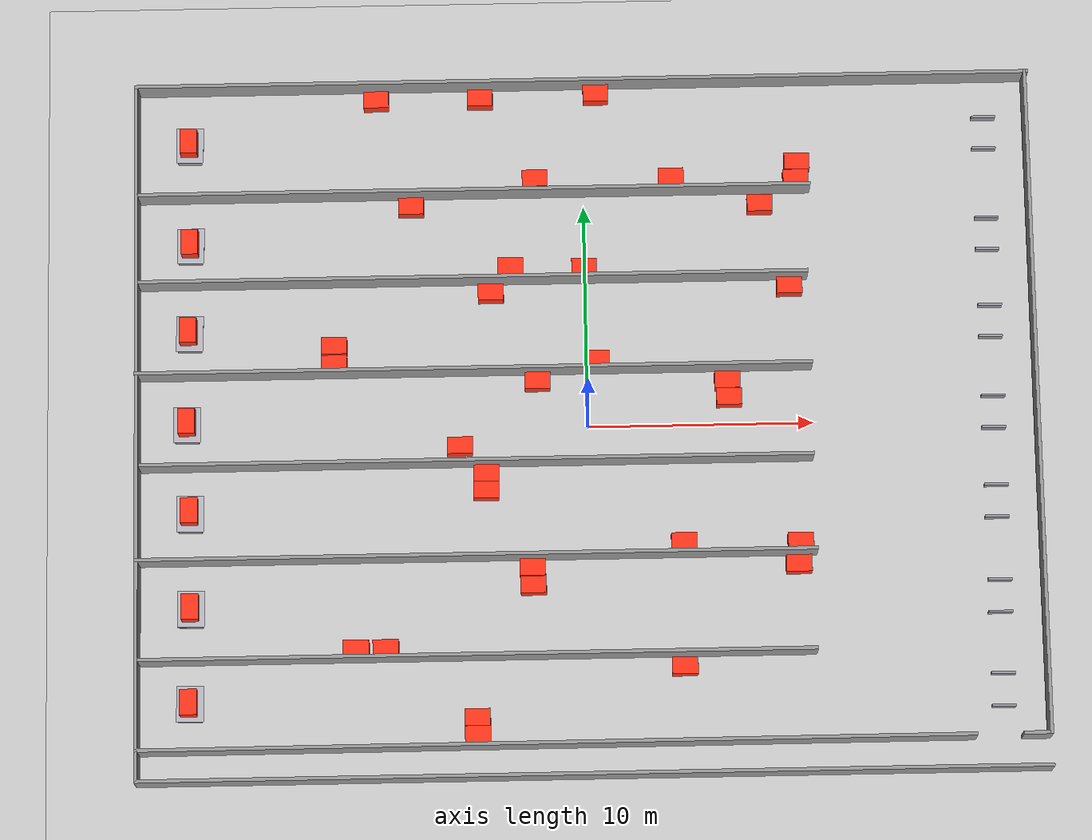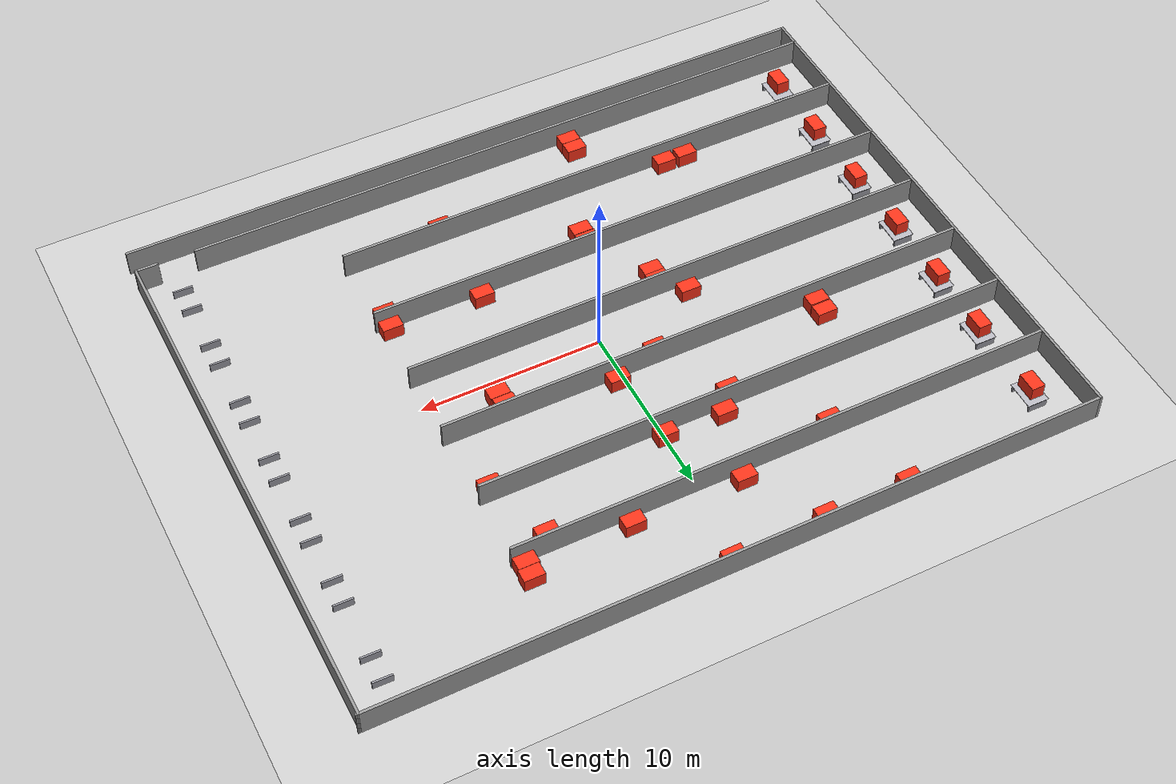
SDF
<sdf version="1.7">
 <world name="default">
  <light name="sun" type="directional">
   <pose>0 0 10 0 -0 0</pose>
   <diffuse>0.8 0.8 0.8 1</diffuse>
   <specular>0.2 0.2 0.2 1</specular>
   <attenuation>
    <range>1000</range>
    <constant>0.9</constant>
    <linear>0.01</linear>
    <quadratic>0.001</quadratic>
   </attenuation>
   <direction>-0.5 0.1 -0.9</direction>
   <spot><inner_angle>0</inner_angle><outer_angle>0</outer_angle><falloff>0</falloff></spot>
  </light>
  <model name="ground_plane">
   <static>1</static>
   <link name="link">
    <collision name="collision">
     <geometry><plane><normal>0 0 1</normal><size>100 100</size></plane></geometry>
     <surface>
      <contact><collide_bitmask>65535</collide_bitmask></contact>
      <friction>
       <ode><mu>200</mu><mu2>200</mu2><fdir1>0 0 0</fdir1><slip1>0</slip1><slip2>0</slip2></ode>
       <torsional>
        <coefficient>1</coefficient>
        <use_patch_radius>1</use_patch_radius>
        <patch_radius>0.1</patch_radius>
        <ode><slip>0</slip></ode>
       </torsional>
      </friction>
     </surface>
    </collision>
    <visual name="visual">
     <cast_shadows>0</cast_shadows>
     <geometry><plane><normal>0 0 1</normal><size>100 100</size></plane></geometry>
     <material>
      <script><uri>file://media/materials/scripts/gazebo.material</uri><name>Gazebo/Grey</name></script>
     </material>
    </visual>
   </link>
  </model>
  <gravity>0 0 -9.8</gravity>
  <magnetic_field>6e-06 2.3e-05 -4.2e-05</magnetic_field>
  <atmosphere type="adiabatic"/>
  <physics type="ode">
   <max_step_size>0.001</max_step_size>
   <real_time_factor>1</real_time_factor>
   <real_time_update_rate>1000</real_time_update_rate>
  </physics>
  <scene><ambient>0.4 0.4 0.4 1</ambient><background>0.7 0.7 0.7 1</background><shadows>1</shadows></scene>
  <spherical_coordinates>
   <surface_model>EARTH_WGS84</surface_model>
   <latitude_deg>0</latitude_deg>
   <longitude_deg>0</longitude_deg>
   <elevation>0</elevation>
   <heading_deg>0</heading_deg>
  </spherical_coordinates>
  <model name="factory_depo">
   <pose>-0.011575 -0.0218 -0.015891 0 -0 0</pose>
   <link name="Wall_11">
    <pose>0.00391 -14.2501 0 0 -0 0.001782</pose>
    <visual name="Wall_11_Visual_0">
     <pose>-1.64591 0 0.75 0 -0 0</pose>
     <geometry><box><size>36.7082 0.15 1.5</size></box></geometry>
     <material>
      <script><uri>file://media/materials/scripts/gazebo.material</uri><name>Gazebo/Grey</name></script>
      <ambient>1 1 1 1</ambient>
     </material>
     <meta><layer>0</layer></meta>
    </visual>
    <collision name="Wall_11_Collision_0">
     <geometry><box><size>36.7082 0.15 1.5</size></box></geometry>
     <pose>-1.64591 0 0.75 0 -0 0</pose>
     <surface><friction><ode><mu>10</mu><mu2>10</mu2><slip1>0</slip1><slip2>0</slip2></ode></friction></surface>
    </collision>
    <visual name="Wall_11_Visual_1">
     <pose>19.3541 0 0.75 0 -0 0</pose>
     <geometry><box><size>1.29181 0.15 1.5</size></box></geometry>
     <material>
      <script><uri>file://media/materials/scripts/gazebo.material</uri><name>Gazebo/Grey</name></script>
      <ambient>1 1 1 1</ambient>
     </material>
     <meta><layer>0</layer></meta>
    </visual>
    <collision name="Wall_11_Collision_1">
     <geometry><box><size>1.29181 0.15 1.5</size></box></geometry>
     <pose>19.3541 0 0.75 0 -0 0</pose>
     <surface><friction><ode><mu>10</mu><mu2>10</mu2><slip1>0</slip1><slip2>0</slip2></ode></friction></surface>
    </collision>
   </link>
   <link name="Wall_13">
    <collision name="Wall_13_Collision">
     <geometry><box><size>30 0.15 1.5</size></box></geometry>
     <pose>0 0 0.75 0 -0 0</pose>
     <surface><friction><ode><mu>10</mu><mu2>10</mu2><slip1>0</slip1><slip2>0</slip2></ode></friction></surface>
    </collision>
    <visual name="Wall_13_Visual">
     <pose>0 0 0.75 0 -0 0</pose>
     <geometry><box><size>30 0.15 1.5</size></box></geometry>
     <material>
      <script><uri>file://media/materials/scripts/gazebo.material</uri><name>Gazebo/Grey</name></script>
      <ambient>1 1 1 1</ambient>
     </material>
     <meta><layer>0</layer></meta>
    </visual>
    <pose>19.8934 0.710432 0 0 -0 1.57317</pose>
   </link>
   <link name="Wall_15">
    <collision name="Wall_15_Collision">
     <geometry><box><size>40 0.15 1.5</size></box></geometry>
     <pose>0 0 0.75 0 -0 0</pose>
     <surface><friction><ode><mu>10</mu><mu2>10</mu2><slip1>0</slip1><slip2>0</slip2></ode></friction></surface>
    </collision>
    <visual name="Wall_15_Visual">
     <pose>0 0 0.75 0 -0 0</pose>
     <geometry><box><size>40 0.15 1.5</size></box></geometry>
     <material>
      <script><uri>file://media/materials/scripts/gazebo.material</uri><name>Gazebo/Grey</name></script>
      <ambient>1 1 1 1</ambient>
     </material>
     <meta><layer>0</layer></meta>
    </visual>
    <pose>0.00391 15.6354 0 0 -0 0</pose>
   </link>
   <link name="Wall_27">
    <collision name="Wall_27_Collision">
     <geometry><box><size>30 0.15 1.5</size></box></geometry>
     <pose>0 0 0.75 0 -0 0</pose>
     <surface><friction><ode><mu>10</mu><mu2>10</mu2><slip1>0</slip1><slip2>0</slip2></ode></friction></surface>
    </collision>
    <visual name="Wall_27_Visual">
     <pose>0 0 0.75 0 -0 0</pose>
     <geometry><box><size>30 0.15 1.5</size></box></geometry>
     <material>
      <script><uri>file://media/materials/scripts/gazebo.material</uri><name>Gazebo/Grey</name></script>
      <ambient>1 1 1 1</ambient>
     </material>
     <meta><layer>0</layer></meta>
    </visual>
    <pose>-4.88109 10.6354 0 0 -0 0</pose>
   </link>
   <link name="Wall_31">
    <collision name="Wall_31_Collision">
     <geometry><box><size>29.75 0.15 1.5</size></box></geometry>
     <pose>0 0 0.75 0 -0 0</pose>
     <surface><friction><ode><mu>10</mu><mu2>10</mu2><slip1>0</slip1><slip2>0</slip2></ode></friction></surface>
    </collision>
    <visual name="Wall_31_Visual">
     <pose>0 0 0.75 0 -0 0</pose>
     <geometry><box><size>29.75 0.15 1.5</size></box></geometry>
     <material>
      <script><uri>file://media/materials/scripts/gazebo.material</uri><name>Gazebo/Grey</name></script>
      <ambient>1 1 1 1</ambient>
     </material>
     <meta><layer>0</layer></meta>
    </visual>
    <pose>-4.96609 6.64743 0 0 -0 0</pose>
   </link>
   <link name="Wall_33">
    <collision name="Wall_33_Collision">
     <geometry><box><size>30 0.15 1.5</size></box></geometry>
     <pose>0 0 0.75 0 -0 0</pose>
     <surface><friction><ode><mu>10</mu><mu2>10</mu2><slip1>0</slip1><slip2>0</slip2></ode></friction></surface>
    </collision>
    <visual name="Wall_33_Visual">
     <pose>0 0 0.75 0 -0 0</pose>
     <geometry><box><size>30 0.15 1.5</size></box></geometry>
     <material>
      <script><uri>file://media/materials/scripts/gazebo.material</uri><name>Gazebo/Grey</name></script>
      <ambient>1 1 1 1</ambient>
     </material>
     <meta><layer>0</layer></meta>
    </visual>
    <pose>-5.00409 2.49743 0 0 -0 0</pose>
   </link>
   <link name="Wall_35">
    <collision name="Wall_35_Collision">
     <geometry><box><size>29.75 0.15 1.5</size></box></geometry>
     <pose>0 0 0.75 0 -0 0</pose>
     <surface><friction><ode><mu>10</mu><mu2>10</mu2><slip1>0</slip1><slip2>0</slip2></ode></friction></surface>
    </collision>
    <visual name="Wall_35_Visual">
     <pose>0 0 0.75 0 -0 0</pose>
     <geometry><box><size>29.75 0.15 1.5</size></box></geometry>
     <material>
      <script><uri>file://media/materials/scripts/gazebo.material</uri><name>Gazebo/Grey</name></script>
      <ambient>1 1 1 1</ambient>
     </material>
     <meta><layer>0</layer></meta>
    </visual>
    <pose>-4.92909 -1.64033 0 0 -0 0</pose>
   </link>
   <link name="Wall_38">
    <collision name="Wall_38_Collision">
     <geometry><box><size>30 0.15 1.5</size></box></geometry>
     <pose>0 0 0.75 0 -0 0</pose>
     <surface><friction><ode><mu>10</mu><mu2>10</mu2><slip1>0</slip1><slip2>0</slip2></ode></friction></surface>
    </collision>
    <visual name="Wall_38_Visual">
     <pose>0 0 0.75 0 -0 0</pose>
     <geometry><box><size>30 0.15 1.5</size></box></geometry>
     <material>
      <script><uri>file://media/materials/scripts/gazebo.material</uri><name>Gazebo/Grey</name></script>
      <ambient>1 1 1 1</ambient>
     </material>
     <meta><layer>0</layer></meta>
    </visual>
    <pose>-4.98909 -5.87657 0 0 -0 0</pose>
   </link>
   <link name="Wall_41">
    <collision name="Wall_41_Collision">
     <geometry><box><size>29.75 0.15 1.5</size></box></geometry>
     <pose>0 0 0.75 0 -0 0</pose>
     <surface><friction><ode><mu>10</mu><mu2>10</mu2><slip1>0</slip1><slip2>0</slip2></ode></friction></surface>
    </collision>
    <visual name="Wall_41_Visual">
     <pose>0 0 0.75 0 -0 0</pose>
     <geometry><box><size>29.75 0.15 1.5</size></box></geometry>
     <material>
      <script><uri>file://media/materials/scripts/gazebo.material</uri><name>Gazebo/Grey</name></script>
      <ambient>1 1 1 1</ambient>
     </material>
     <meta><layer>0</layer></meta>
    </visual>
    <pose>-4.99109 -10.3066 0 0 -0 0</pose>
   </link>
   <link name="Wall_43">
    <collision name="Wall_43_Collision">
     <geometry><box><size>1.5 0.15 1.5</size></box></geometry>
     <pose>0 0 0.75 0 -0 0</pose>
     <surface><friction><ode><mu>10</mu><mu2>10</mu2><slip1>0</slip1><slip2>0</slip2></ode></friction></surface>
    </collision>
    <visual name="Wall_43_Visual">
     <pose>0 0 0.75 0 -0 0</pose>
     <geometry><box><size>1.5 0.15 1.5</size></box></geometry>
     <material>
      <script><uri>file://media/materials/scripts/gazebo.material</uri><name>Gazebo/Grey</name></script>
      <ambient>1 1 1 1</ambient>
     </material>
     <meta><layer>0</layer></meta>
    </visual>
    <pose>-19.9211 -14.9606 0 0 -0 -1.5708</pose>
   </link>
   <link name="Wall_45">
    <collision name="Wall_45_Collision">
     <geometry><box><size>40 0.15 1.5</size></box></geometry>
     <pose>0 0 0.75 0 -0 0</pose>
     <surface><friction><ode><mu>10</mu><mu2>10</mu2><slip1>0</slip1><slip2>0</slip2></ode></friction></surface>
    </collision>
    <visual name="Wall_45_Visual">
     <pose>0 0 0.75 0 -0 0</pose>
     <geometry><box><size>40 0.15 1.5</size></box></geometry>
     <material>
      <script><uri>file://media/materials/scripts/gazebo.material</uri><name>Gazebo/Grey</name></script>
      <ambient>1 1 1 1</ambient>
     </material>
     <meta><layer>0</layer></meta>
    </visual>
    <pose>0.00391 -15.6356 0 0 -0 0</pose>
   </link>
   <link name="Wall_9">
    <collision name="Wall_9_Collision">
     <geometry><box><size>30.071 0.15 1.5</size></box></geometry>
     <pose>0 0 0.75 0 -0 0</pose>
     <surface><friction><ode><mu>10</mu><mu2>10</mu2><slip1>0</slip1><slip2>0</slip2></ode></friction></surface>
    </collision>
    <visual name="Wall_9_Visual">
     <pose>0 0 0.75 0 -0 0</pose>
     <geometry><box><size>30.071 0.15 1.5</size></box></geometry>
     <material>
      <script><uri>file://media/materials/scripts/gazebo.material</uri><name>Gazebo/Grey</name></script>
      <ambient>1 1 1 1</ambient>
     </material>
     <meta><layer>0</layer></meta>
    </visual>
    <pose>-19.9211 0.674932 0 0 -0 1.5708</pose>
   </link>
   <static>1</static>
  </model>
  <model name="stand_1_legs">
   <static>1</static>
   <link name="walls_link">
    <collision name="left_wall_col">
     <pose>0.72 0 0.225 0 -0 0</pose>
     <geometry><box><size>0.1 1.06 0.45</size></box></geometry>
     <surface><friction><ode><mu>10</mu><mu2>10</mu2><slip1>0</slip1><slip2>0</slip2></ode></friction></surface>
    </collision>
    <visual name="left_wall_vis">
     <pose>0.72 0 0.225 0 -0 0</pose>
     <geometry><box><size>0.1 1.06 0.45</size></box></geometry>
     <material>
      <ambient>0.6 0.6 0.63 1</ambient>
      <diffuse>0.6 0.6 0.63 1</diffuse>
      <specular>0.3 0.3 0.3 1</specular>
     </material>
    </visual>
    <collision name="right_wall_col">
     <pose>-0.72 0 0.225 0 -0 0</pose>
     <geometry><box><size>0.1 1.06 0.45</size></box></geometry>
     <surface><friction><ode><mu>10</mu><mu2>10</mu2><slip1>0</slip1><slip2>0</slip2></ode></friction></surface>
    </collision>
    <visual name="right_wall_vis">
     <pose>-0.72 0 0.225 0 -0 0</pose>
     <geometry><box><size>0.1 1.06 0.45</size></box></geometry>
     <material>
      <ambient>0.6 0.6 0.63 1</ambient>
      <diffuse>0.6 0.6 0.63 1</diffuse>
      <specular>0.3 0.3 0.3 1</specular>
     </material>
    </visual>
    <inertial>
     <mass>25</mass>
     <inertia><ixx>1.4</ixx><iyy>2.1</iyy><izz>3.2</izz><ixy>0</ixy><ixz>0</ixz><iyz>0</iyz></inertia>
    </inertial>
   </link>
   <pose>-17.6281 4.46335 -3e-06 1.2e-05 1e-06 -1.58718</pose>
  </model>
  <model name="stand_1_top">
   <static>0</static>
   <link name="top_link">
    <collision name="top_plate_col">
     <pose>0 0 0.46 0 -0 0</pose>
     <geometry><box><size>1.6 1.2 0.02</size></box></geometry>
     <surface><friction><ode><mu>10</mu><mu2>10</mu2><slip1>0</slip1><slip2>0</slip2></ode></friction></surface>
    </collision>
    <visual name="top_plate_vis">
     <pose>0 0 0.46 0 -0 0</pose>
     <geometry><box><size>1.6 1.2 0.02</size></box></geometry>
     <material>
      <ambient>0.72 0.72 0.75 1</ambient>
      <diffuse>0.72 0.72 0.75 1</diffuse>
      <specular>0.5 0.5 0.5 1</specular>
     </material>
    </visual>
    <inertial>
     <mass>10</mass>
     <inertia><ixx>0.8</ixx><iyy>1.3</iyy><izz>2</izz><ixy>0</ixy><ixz>0</ixz><iyz>0</iyz></inertia>
    </inertial>
   </link>
   <pose>-17.6282 4.46319 -1.1e-05 1.2e-05 -1e-05 -1.58698</pose>
  </model>
  <model name="stand_1_clone_legs">
   <static>1</static>
   <link name="walls_link">
    <collision name="left_wall_col">
     <pose>0.72 0 0.225 0 -0 0</pose>
     <geometry><box><size>0.1 1.06 0.45</size></box></geometry>
     <surface><friction><ode><mu>10</mu><mu2>10</mu2><slip1>0</slip1><slip2>0</slip2></ode></friction></surface>
    </collision>
    <visual name="left_wall_vis">
     <pose>0.72 0 0.225 0 -0 0</pose>
     <geometry><box><size>0.1 1.06 0.45</size></box></geometry>
     <material>
      <ambient>0.6 0.6 0.63 1</ambient>
      <diffuse>0.6 0.6 0.63 1</diffuse>
      <specular>0.3 0.3 0.3 1</specular>
     </material>
    </visual>
    <collision name="right_wall_col">
     <pose>-0.72 0 0.225 0 -0 0</pose>
     <geometry><box><size>0.1 1.06 0.45</size></box></geometry>
     <surface><friction><ode><mu>10</mu><mu2>10</mu2><slip1>0</slip1><slip2>0</slip2></ode></friction></surface>
    </collision>
    <visual name="right_wall_vis">
     <pose>-0.72 0 0.225 0 -0 0</pose>
     <geometry><box><size>0.1 1.06 0.45</size></box></geometry>
     <material>
      <ambient>0.6 0.6 0.63 1</ambient>
      <diffuse>0.6 0.6 0.63 1</diffuse>
      <specular>0.3 0.3 0.3 1</specular>
     </material>
    </visual>
    <inertial>
     <mass>25</mass>
     <inertia><ixx>1.4</ixx><iyy>2.1</iyy><izz>3.2</izz><ixy>0</ixy><ixz>0</ixz><iyz>0</iyz></inertia>
    </inertial>
   </link>
   <pose>-17.5795 8.4682 -2e-06 5e-06 -0 -1.58628</pose>
  </model>
  <model name="stand_1_clone_top">
   <static>0</static>
   <link name="top_link">
    <collision name="top_plate_col">
     <pose>0 0 0.46 0 -0 0</pose>
     <geometry><box><size>1.6 1.2 0.02</size></box></geometry>
     <surface><friction><ode><mu>10</mu><mu2>10</mu2><slip1>0</slip1><slip2>0</slip2></ode></friction></surface>
    </collision>
    <visual name="top_plate_vis">
     <pose>0 0 0.46 0 -0 0</pose>
     <geometry><box><size>1.6 1.2 0.02</size></box></geometry>
     <material>
      <ambient>0.72 0.72 0.75 1</ambient>
      <diffuse>0.72 0.72 0.75 1</diffuse>
      <specular>0.5 0.5 0.5 1</specular>
     </material>
    </visual>
    <inertial>
     <mass>10</mass>
     <inertia><ixx>0.8</ixx><iyy>1.3</iyy><izz>2</izz><ixy>0</ixy><ixz>0</ixz><iyz>0</iyz></inertia>
    </inertial>
   </link>
   <pose>-17.5797 8.46804 -2e-06 -1e-05 1.3e-05 -1.58617</pose>
  </model>
  <model name="stand_1_clone_0_legs">
   <static>1</static>
   <link name="walls_link">
    <collision name="left_wall_col">
     <pose>0.72 0 0.225 0 -0 0</pose>
     <geometry><box><size>0.1 1.06 0.45</size></box></geometry>
     <surface><friction><ode><mu>10</mu><mu2>10</mu2><slip1>0</slip1><slip2>0</slip2></ode></friction></surface>
    </collision>
    <visual name="left_wall_vis">
     <pose>0.72 0 0.225 0 -0 0</pose>
     <geometry><box><size>0.1 1.06 0.45</size></box></geometry>
     <material>
      <ambient>0.6 0.6 0.63 1</ambient>
      <diffuse>0.6 0.6 0.63 1</diffuse>
      <specular>0.3 0.3 0.3 1</specular>
     </material>
    </visual>
    <collision name="right_wall_col">
     <pose>-0.72 0 0.225 0 -0 0</pose>
     <geometry><box><size>0.1 1.06 0.45</size></box></geometry>
     <surface><friction><ode><mu>10</mu><mu2>10</mu2><slip1>0</slip1><slip2>0</slip2></ode></friction></surface>
    </collision>
    <visual name="right_wall_vis">
     <pose>-0.72 0 0.225 0 -0 0</pose>
     <geometry><box><size>0.1 1.06 0.45</size></box></geometry>
     <material>
      <ambient>0.6 0.6 0.63 1</ambient>
      <diffuse>0.6 0.6 0.63 1</diffuse>
      <specular>0.3 0.3 0.3 1</specular>
     </material>
    </visual>
    <inertial>
     <mass>25</mass>
     <inertia><ixx>1.4</ixx><iyy>2.1</iyy><izz>3.2</izz><ixy>0</ixy><ixz>0</ixz><iyz>0</iyz></inertia>
    </inertial>
   </link>
   <pose>-17.6066 13.1094 0 1e-06 0 -1.58633</pose>
  </model>
  <model name="stand_1_clone_0_top">
   <static>0</static>
   <link name="top_link">
    <collision name="top_plate_col">
     <pose>0 0 0.46 0 -0 0</pose>
     <geometry><box><size>1.6 1.2 0.02</size></box></geometry>
     <surface><friction><ode><mu>10</mu><mu2>10</mu2><slip1>0</slip1><slip2>0</slip2></ode></friction></surface>
    </collision>
    <visual name="top_plate_vis">
     <pose>0 0 0.46 0 -0 0</pose>
     <geometry><box><size>1.6 1.2 0.02</size></box></geometry>
     <material>
      <ambient>0.72 0.72 0.75 1</ambient>
      <diffuse>0.72 0.72 0.75 1</diffuse>
      <specular>0.5 0.5 0.5 1</specular>
     </material>
    </visual>
    <inertial>
     <mass>10</mass>
     <inertia><ixx>0.8</ixx><iyy>1.3</iyy><izz>2</izz><ixy>0</ixy><ixz>0</ixz><iyz>0</iyz></inertia>
    </inertial>
   </link>
   <pose>-17.6066 13.1092 -4.4e-05 4.2e-05 8e-06 -1.5862</pose>
  </model>
  <model name="stand_1_clone_1_legs">
   <static>1</static>
   <link name="walls_link">
    <collision name="left_wall_col">
     <pose>0.72 0 0.225 0 -0 0</pose>
     <geometry><box><size>0.1 1.06 0.45</size></box></geometry>
     <surface><friction><ode><mu>10</mu><mu2>10</mu2><slip1>0</slip1><slip2>0</slip2></ode></friction></surface>
    </collision>
    <visual name="left_wall_vis">
     <pose>0.72 0 0.225 0 -0 0</pose>
     <geometry><box><size>0.1 1.06 0.45</size></box></geometry>
     <material>
      <ambient>0.6 0.6 0.63 1</ambient>
      <diffuse>0.6 0.6 0.63 1</diffuse>
      <specular>0.3 0.3 0.3 1</specular>
     </material>
    </visual>
    <collision name="right_wall_col">
     <pose>-0.72 0 0.225 0 -0 0</pose>
     <geometry><box><size>0.1 1.06 0.45</size></box></geometry>
     <surface><friction><ode><mu>10</mu><mu2>10</mu2><slip1>0</slip1><slip2>0</slip2></ode></friction></surface>
    </collision>
    <visual name="right_wall_vis">
     <pose>-0.72 0 0.225 0 -0 0</pose>
     <geometry><box><size>0.1 1.06 0.45</size></box></geometry>
     <material>
      <ambient>0.6 0.6 0.63 1</ambient>
      <diffuse>0.6 0.6 0.63 1</diffuse>
      <specular>0.3 0.3 0.3 1</specular>
     </material>
    </visual>
    <inertial>
     <mass>25</mass>
     <inertia><ixx>1.4</ixx><iyy>2.1</iyy><izz>3.2</izz><ixy>0</ixy><ixz>0</ixz><iyz>0</iyz></inertia>
    </inertial>
   </link>
   <pose>-17.7499 0.31944 -2e-06 5e-06 -1e-06 -1.58624</pose>
  </model>
  <model name="stand_1_clone_1_top">
   <static>0</static>
   <link name="top_link">
    <collision name="top_plate_col">
     <pose>0 0 0.46 0 -0 0</pose>
     <geometry><box><size>1.6 1.2 0.02</size></box></geometry>
     <surface><friction><ode><mu>10</mu><mu2>10</mu2><slip1>0</slip1><slip2>0</slip2></ode></friction></surface>
    </collision>
    <visual name="top_plate_vis">
     <pose>0 0 0.46 0 -0 0</pose>
     <geometry><box><size>1.6 1.2 0.02</size></box></geometry>
     <material>
      <ambient>0.72 0.72 0.75 1</ambient>
      <diffuse>0.72 0.72 0.75 1</diffuse>
      <specular>0.5 0.5 0.5 1</specular>
     </material>
    </visual>
    <inertial>
     <mass>10</mass>
     <inertia><ixx>0.8</ixx><iyy>1.3</iyy><izz>2</izz><ixy>0</ixy><ixz>0</ixz><iyz>0</iyz></inertia>
    </inertial>
   </link>
   <pose>-17.75 0.31932 -8e-06 -7e-06 -1e-06 -1.58613</pose>
  </model>
  <model name="stand_1_clone_2_legs">
   <static>1</static>
   <link name="walls_link">
    <collision name="left_wall_col">
     <pose>0.72 0 0.225 0 -0 0</pose>
     <geometry><box><size>0.1 1.06 0.45</size></box></geometry>
     <surface><friction><ode><mu>10</mu><mu2>10</mu2><slip1>0</slip1><slip2>0</slip2></ode></friction></surface>
    </collision>
    <visual name="left_wall_vis">
     <pose>0.72 0 0.225 0 -0 0</pose>
     <geometry><box><size>0.1 1.06 0.45</size></box></geometry>
     <material>
      <ambient>0.6 0.6 0.63 1</ambient>
      <diffuse>0.6 0.6 0.63 1</diffuse>
      <specular>0.3 0.3 0.3 1</specular>
     </material>
    </visual>
    <collision name="right_wall_col">
     <pose>-0.72 0 0.225 0 -0 0</pose>
     <geometry><box><size>0.1 1.06 0.45</size></box></geometry>
     <surface><friction><ode><mu>10</mu><mu2>10</mu2><slip1>0</slip1><slip2>0</slip2></ode></friction></surface>
    </collision>
    <visual name="right_wall_vis">
     <pose>-0.72 0 0.225 0 -0 0</pose>
     <geometry><box><size>0.1 1.06 0.45</size></box></geometry>
     <material>
      <ambient>0.6 0.6 0.63 1</ambient>
      <diffuse>0.6 0.6 0.63 1</diffuse>
      <specular>0.3 0.3 0.3 1</specular>
     </material>
    </visual>
    <inertial>
     <mass>25</mass>
     <inertia><ixx>1.4</ixx><iyy>2.1</iyy><izz>3.2</izz><ixy>0</ixy><ixz>0</ixz><iyz>0</iyz></inertia>
    </inertial>
   </link>
   <pose>-17.6177 -3.70917 -5e-06 1.8e-05 -0 -1.58623</pose>
  </model>
  <model name="stand_1_clone_2_top">
   <static>0</static>
   <link name="top_link">
    <collision name="top_plate_col">
     <pose>0 0 0.46 0 -0 0</pose>
     <geometry><box><size>1.6 1.2 0.02</size></box></geometry>
     <surface><friction><ode><mu>10</mu><mu2>10</mu2><slip1>0</slip1><slip2>0</slip2></ode></friction></surface>
    </collision>
    <visual name="top_plate_vis">
     <pose>0 0 0.46 0 -0 0</pose>
     <geometry><box><size>1.6 1.2 0.02</size></box></geometry>
     <material>
      <ambient>0.72 0.72 0.75 1</ambient>
      <diffuse>0.72 0.72 0.75 1</diffuse>
      <specular>0.5 0.5 0.5 1</specular>
     </material>
    </visual>
    <inertial>
     <mass>10</mass>
     <inertia><ixx>0.8</ixx><iyy>1.3</iyy><izz>2</izz><ixy>0</ixy><ixz>0</ixz><iyz>0</iyz></inertia>
    </inertial>
   </link>
   <pose>-17.6177 -3.70921 -7e-05 -2.6e-05 1.6e-05 -1.58613</pose>
  </model>
  <model name="stand_1_clone_3_legs">
   <static>1</static>
   <link name="walls_link">
    <collision name="left_wall_col">
     <pose>0.72 0 0.225 0 -0 0</pose>
     <geometry><box><size>0.1 1.06 0.45</size></box></geometry>
     <surface><friction><ode><mu>10</mu><mu2>10</mu2><slip1>0</slip1><slip2>0</slip2></ode></friction></surface>
    </collision>
    <visual name="left_wall_vis">
     <pose>0.72 0 0.225 0 -0 0</pose>
     <geometry><box><size>0.1 1.06 0.45</size></box></geometry>
     <material>
      <ambient>0.6 0.6 0.63 1</ambient>
      <diffuse>0.6 0.6 0.63 1</diffuse>
      <specular>0.3 0.3 0.3 1</specular>
     </material>
    </visual>
    <collision name="right_wall_col">
     <pose>-0.72 0 0.225 0 -0 0</pose>
     <geometry><box><size>0.1 1.06 0.45</size></box></geometry>
     <surface><friction><ode><mu>10</mu><mu2>10</mu2><slip1>0</slip1><slip2>0</slip2></ode></friction></surface>
    </collision>
    <visual name="right_wall_vis">
     <pose>-0.72 0 0.225 0 -0 0</pose>
     <geometry><box><size>0.1 1.06 0.45</size></box></geometry>
     <material>
      <ambient>0.6 0.6 0.63 1</ambient>
      <diffuse>0.6 0.6 0.63 1</diffuse>
      <specular>0.3 0.3 0.3 1</specular>
     </material>
    </visual>
    <inertial>
     <mass>25</mass>
     <inertia><ixx>1.4</ixx><iyy>2.1</iyy><izz>3.2</izz><ixy>0</ixy><ixz>0</ixz><iyz>0</iyz></inertia>
    </inertial>
   </link>
   <pose>-17.5863 -7.964 -7e-06 0 1.5e-05 -1.58655</pose>
  </model>
  <model name="stand_1_clone_3_top">
   <static>0</static>
   <link name="top_link">
    <collision name="top_plate_col">
     <pose>0 0 0.46 0 -0 0</pose>
     <geometry><box><size>1.6 1.2 0.02</size></box></geometry>
     <surface><friction><ode><mu>10</mu><mu2>10</mu2><slip1>0</slip1><slip2>0</slip2></ode></friction></surface>
    </collision>
    <visual name="top_plate_vis">
     <pose>0 0 0.46 0 -0 0</pose>
     <geometry><box><size>1.6 1.2 0.02</size></box></geometry>
     <material>
      <ambient>0.72 0.72 0.75 1</ambient>
      <diffuse>0.72 0.72 0.75 1</diffuse>
      <specular>0.5 0.5 0.5 1</specular>
     </material>
    </visual>
    <inertial>
     <mass>10</mass>
     <inertia><ixx>0.8</ixx><iyy>1.3</iyy><izz>2</izz><ixy>0</ixy><ixz>0</ixz><iyz>0</iyz></inertia>
    </inertial>
   </link>
   <pose>-17.5863 -7.96415 -1.4e-05 -7e-06 2e-05 -1.58646</pose>
  </model>
  <model name="stand_1_clone_4_legs">
   <static>1</static>
   <link name="walls_link">
    <collision name="left_wall_col">
     <pose>0.72 0 0.225 0 -0 0</pose>
     <geometry><box><size>0.1 1.06 0.45</size></box></geometry>
     <surface><friction><ode><mu>10</mu><mu2>10</mu2><slip1>0</slip1><slip2>0</slip2></ode></friction></surface>
    </collision>
    <visual name="left_wall_vis">
     <pose>0.72 0 0.225 0 -0 0</pose>
     <geometry><box><size>0.1 1.06 0.45</size></box></geometry>
     <material>
      <ambient>0.6 0.6 0.63 1</ambient>
      <diffuse>0.6 0.6 0.63 1</diffuse>
      <specular>0.3 0.3 0.3 1</specular>
     </material>
    </visual>
    <collision name="right_wall_col">
     <pose>-0.72 0 0.225 0 -0 0</pose>
     <geometry><box><size>0.1 1.06 0.45</size></box></geometry>
     <surface><friction><ode><mu>10</mu><mu2>10</mu2><slip1>0</slip1><slip2>0</slip2></ode></friction></surface>
    </collision>
    <visual name="right_wall_vis">
     <pose>-0.72 0 0.225 0 -0 0</pose>
     <geometry><box><size>0.1 1.06 0.45</size></box></geometry>
     <material>
      <ambient>0.6 0.6 0.63 1</ambient>
      <diffuse>0.6 0.6 0.63 1</diffuse>
      <specular>0.3 0.3 0.3 1</specular>
     </material>
    </visual>
    <inertial>
     <mass>25</mass>
     <inertia><ixx>1.4</ixx><iyy>2.1</iyy><izz>3.2</izz><ixy>0</ixy><ixz>0</ixz><iyz>0</iyz></inertia>
    </inertial>
   </link>
   <pose>-17.6339 -12.1584 0 3e-06 2e-06 -1.58716</pose>
  </model>
  <model name="stand_1_clone_4_top">
   <static>0</static>
   <link name="top_link">
    <collision name="top_plate_col">
     <pose>0 0 0.46 0 -0 0</pose>
     <geometry><box><size>1.6 1.2 0.02</size></box></geometry>
     <surface><friction><ode><mu>10</mu><mu2>10</mu2><slip1>0</slip1><slip2>0</slip2></ode></friction></surface>
    </collision>
    <visual name="top_plate_vis">
     <pose>0 0 0.46 0 -0 0</pose>
     <geometry><box><size>1.6 1.2 0.02</size></box></geometry>
     <material>
      <ambient>0.72 0.72 0.75 1</ambient>
      <diffuse>0.72 0.72 0.75 1</diffuse>
      <specular>0.5 0.5 0.5 1</specular>
     </material>
    </visual>
    <inertial>
     <mass>10</mass>
     <inertia><ixx>0.8</ixx><iyy>1.3</iyy><izz>2</izz><ixy>0</ixy><ixz>0</ixz><iyz>0</iyz></inertia>
    </inertial>
   </link>
   <pose>-17.634 -12.1586 -1.1e-05 7e-06 1.5e-05 -1.58702</pose>
  </model>
  <model name="payload_box">
   <link name="link">
    <inertial>
     <mass>15</mass>
     <inertia><ixx>2.32332</ixx><ixy>0</ixy><ixz>0</ixz><iyy>1.43272</iyy><iyz>0</iyz><izz>2.2858</izz></inertia>
    </inertial>
    <visual name="visual">
     <geometry><box><size>0.747047 1.12719 0.766877</size></box></geometry>
     <material>
      <script><name>Gazebo/Grey</name><uri>file://media/materials/scripts/gazebo.material</uri></script>
      <shader type="pixel"><normal_map>__default__</normal_map></shader>
      <ambient>1 0.2 0.1 0</ambient>
      <diffuse>0.7 0.7 0.7 1</diffuse>
      <specular>0.01 0.01 0.01 1</specular>
      <emissive>0 0 0 1</emissive>
     </material>
    </visual>
    <collision name="collision">
     <geometry><box><size>0.747047 1.12719 0.766877</size></box></geometry>
     <surface>
      <friction>
       <ode><mu>1</mu><mu2>1</mu2><fdir1>0 0 0</fdir1><slip1>0</slip1><slip2>0</slip2></ode>
       <torsional>
        <coefficient>1</coefficient>
        <patch_radius>0</patch_radius>
        <surface_radius>0</surface_radius>
        <use_patch_radius>1</use_patch_radius>
        <ode><slip>0</slip></ode>
       </torsional>
      </friction>
      <bounce><restitution_coefficient>0</restitution_coefficient><threshold>1e+06</threshold></bounce>
      <contact>
       <collide_without_contact>0</collide_without_contact>
       <collide_without_contact_bitmask>1</collide_without_contact_bitmask>
       <collide_bitmask>1</collide_bitmask>
       <ode>
        <soft_cfm>0</soft_cfm>
        <soft_erp>0.2</soft_erp>
        <kp>1e+13</kp>
        <kd>1</kd>
        <max_vel>0.01</max_vel>
        <min_depth>0</min_depth>
       </ode>
       <bullet>
        <split_impulse>1</split_impulse>
        <split_impulse_penetration_threshold>-0.01</split_impulse_penetration_threshold>
        <soft_cfm>0</soft_cfm>
        <soft_erp>0.2</soft_erp>
        <kp>1e+13</kp>
        <kd>1</kd>
       </bullet>
      </contact>
     </surface>
    </collision>
   </link>
   <static>0</static>
   <pose>-17.6588 -12.1948 0.997451 2.3e-05 4.6e-05 -0.002745</pose>
  </model>
  <model name="payload_box_clone">
   <link name="link">
    <inertial>
     <mass>15</mass>
     <inertia><ixx>2.32332</ixx><ixy>0</ixy><ixz>0</ixz><iyy>1.43272</iyy><iyz>0</iyz><izz>2.2858</izz></inertia>
    </inertial>
    <visual name="visual">
     <geometry><box><size>0.747047 1.12719 0.766877</size></box></geometry>
     <material>
      <script><name>Gazebo/Grey</name><uri>file://media/materials/scripts/gazebo.material</uri></script>
      <shader type="pixel"><normal_map>__default__</normal_map></shader>
      <ambient>1 0.2 0.1 0</ambient>
      <diffuse>0.7 0.7 0.7 1</diffuse>
      <specular>0.01 0.01 0.01 1</specular>
      <emissive>0 0 0 1</emissive>
     </material>
    </visual>
    <collision name="collision">
     <geometry><box><size>0.747047 1.12719 0.766877</size></box></geometry>
     <surface>
      <friction>
       <ode><mu>1</mu><mu2>1</mu2><fdir1>0 0 0</fdir1><slip1>0</slip1><slip2>0</slip2></ode>
       <torsional>
        <coefficient>1</coefficient>
        <patch_radius>0</patch_radius>
        <surface_radius>0</surface_radius>
        <use_patch_radius>1</use_patch_radius>
        <ode><slip>0</slip></ode>
       </torsional>
      </friction>
      <bounce><restitution_coefficient>0</restitution_coefficient><threshold>1e+06</threshold></bounce>
      <contact>
       <collide_without_contact>0</collide_without_contact>
       <collide_without_contact_bitmask>1</collide_without_contact_bitmask>
       <collide_bitmask>1</collide_bitmask>
       <ode>
        <soft_cfm>0</soft_cfm>
        <soft_erp>0.2</soft_erp>
        <kp>1e+13</kp>
        <kd>1</kd>
        <max_vel>0.01</max_vel>
        <min_depth>0</min_depth>
       </ode>
       <bullet>
        <split_impulse>1</split_impulse>
        <split_impulse_penetration_threshold>-0.01</split_impulse_penetration_threshold>
        <soft_cfm>0</soft_cfm>
        <soft_erp>0.2</soft_erp>
        <kp>1e+13</kp>
        <kd>1</kd>
       </bullet>
      </contact>
     </surface>
    </collision>
   </link>
   <static>0</static>
   <pose>-17.5836 -7.98368 0.997363 7e-06 -1e-05 -0.00279</pose>
  </model>
  <model name="payload_box_clone_0">
   <link name="link">
    <inertial>
     <mass>15</mass>
     <inertia><ixx>2.32332</ixx><ixy>0</ixy><ixz>0</ixz><iyy>1.43272</iyy><iyz>0</iyz><izz>2.2858</izz></inertia>
    </inertial>
    <visual name="visual">
     <geometry><box><size>0.747047 1.12719 0.766877</size></box></geometry>
     <material>
      <script><name>Gazebo/Grey</name><uri>file://media/materials/scripts/gazebo.material</uri></script>
      <shader type="pixel"><normal_map>__default__</normal_map></shader>
      <ambient>1 0.2 0.1 0</ambient>
      <diffuse>0.7 0.7 0.7 1</diffuse>
      <specular>0.01 0.01 0.01 1</specular>
      <emissive>0 0 0 1</emissive>
     </material>
    </visual>
    <collision name="collision">
     <geometry><box><size>0.747047 1.12719 0.766877</size></box></geometry>
     <surface>
      <friction>
       <ode><mu>1</mu><mu2>1</mu2><fdir1>0 0 0</fdir1><slip1>0</slip1><slip2>0</slip2></ode>
       <torsional>
        <coefficient>1</coefficient>
        <patch_radius>0</patch_radius>
        <surface_radius>0</surface_radius>
        <use_patch_radius>1</use_patch_radius>
        <ode><slip>0</slip></ode>
       </torsional>
      </friction>
      <bounce><restitution_coefficient>0</restitution_coefficient><threshold>1e+06</threshold></bounce>
      <contact>
       <collide_without_contact>0</collide_without_contact>
       <collide_without_contact_bitmask>1</collide_without_contact_bitmask>
       <collide_bitmask>1</collide_bitmask>
       <ode>
        <soft_cfm>0</soft_cfm>
        <soft_erp>0.2</soft_erp>
        <kp>1e+13</kp>
        <kd>1</kd>
        <max_vel>0.01</max_vel>
        <min_depth>0</min_depth>
       </ode>
       <bullet>
        <split_impulse>1</split_impulse>
        <split_impulse_penetration_threshold>-0.01</split_impulse_penetration_threshold>
        <soft_cfm>0</soft_cfm>
        <soft_erp>0.2</soft_erp>
        <kp>1e+13</kp>
        <kd>1</kd>
       </bullet>
      </contact>
     </surface>
    </collision>
   </link>
   <static>0</static>
   <pose>-17.6151 -3.68901 0.99734 3e-05 -1.6e-05 -0.000232</pose>
  </model>
  <model name="payload_box_clone_1">
   <link name="link">
    <inertial>
     <mass>15</mass>
     <inertia><ixx>2.32332</ixx><ixy>0</ixy><ixz>0</ixz><iyy>1.43272</iyy><iyz>0</iyz><izz>2.2858</izz></inertia>
    </inertial>
    <visual name="visual">
     <geometry><box><size>0.747047 1.12719 0.766877</size></box></geometry>
     <material>
      <script><name>Gazebo/Grey</name><uri>file://media/materials/scripts/gazebo.material</uri></script>
      <shader type="pixel"><normal_map>__default__</normal_map></shader>
      <ambient>1 0.2 0.1 0</ambient>
      <diffuse>0.7 0.7 0.7 1</diffuse>
      <specular>0.01 0.01 0.01 1</specular>
      <emissive>0 0 0 1</emissive>
     </material>
    </visual>
    <collision name="collision">
     <geometry><box><size>0.747047 1.12719 0.766877</size></box></geometry>
     <surface>
      <friction>
       <ode><mu>1</mu><mu2>1</mu2><fdir1>0 0 0</fdir1><slip1>0</slip1><slip2>0</slip2></ode>
       <torsional>
        <coefficient>1</coefficient>
        <patch_radius>0</patch_radius>
        <surface_radius>0</surface_radius>
        <use_patch_radius>1</use_patch_radius>
        <ode><slip>0</slip></ode>
       </torsional>
      </friction>
      <bounce><restitution_coefficient>0</restitution_coefficient><threshold>1e+06</threshold></bounce>
      <contact>
       <collide_without_contact>0</collide_without_contact>
       <collide_without_contact_bitmask>1</collide_without_contact_bitmask>
       <collide_bitmask>1</collide_bitmask>
       <ode>
        <soft_cfm>0</soft_cfm>
        <soft_erp>0.2</soft_erp>
        <kp>1e+13</kp>
        <kd>1</kd>
        <max_vel>0.01</max_vel>
        <min_depth>0</min_depth>
       </ode>
       <bullet>
        <split_impulse>1</split_impulse>
        <split_impulse_penetration_threshold>-0.01</split_impulse_penetration_threshold>
        <soft_cfm>0</soft_cfm>
        <soft_erp>0.2</soft_erp>
        <kp>1e+13</kp>
        <kd>1</kd>
       </bullet>
      </contact>
     </surface>
    </collision>
   </link>
   <static>0</static>
   <pose>-17.72 0.323062 0.997401 -3.7e-05 4e-06 -0.001268</pose>
  </model>
  <model name="payload_box_clone_2">
   <link name="link">
    <inertial>
     <mass>15</mass>
     <inertia><ixx>2.32332</ixx><ixy>0</ixy><ixz>0</ixz><iyy>1.43272</iyy><iyz>0</iyz><izz>2.2858</izz></inertia>
    </inertial>
    <visual name="visual">
     <geometry><box><size>0.747047 1.12719 0.766877</size></box></geometry>
     <material>
      <script><name>Gazebo/Grey</name><uri>file://media/materials/scripts/gazebo.material</uri></script>
      <shader type="pixel"><normal_map>__default__</normal_map></shader>
      <ambient>1 0.2 0.1 0</ambient>
      <diffuse>0.7 0.7 0.7 1</diffuse>
      <specular>0.01 0.01 0.01 1</specular>
      <emissive>0 0 0 1</emissive>
     </material>
    </visual>
    <collision name="collision">
     <geometry><box><size>0.747047 1.12719 0.766877</size></box></geometry>
     <surface>
      <friction>
       <ode><mu>1</mu><mu2>1</mu2><fdir1>0 0 0</fdir1><slip1>0</slip1><slip2>0</slip2></ode>
       <torsional>
        <coefficient>1</coefficient>
        <patch_radius>0</patch_radius>
        <surface_radius>0</surface_radius>
        <use_patch_radius>1</use_patch_radius>
        <ode><slip>0</slip></ode>
       </torsional>
      </friction>
      <bounce><restitution_coefficient>0</restitution_coefficient><threshold>1e+06</threshold></bounce>
      <contact>
       <collide_without_contact>0</collide_without_contact>
       <collide_without_contact_bitmask>1</collide_without_contact_bitmask>
       <collide_bitmask>1</collide_bitmask>
       <ode>
        <soft_cfm>0</soft_cfm>
        <soft_erp>0.2</soft_erp>
        <kp>1e+13</kp>
        <kd>1</kd>
        <max_vel>0.01</max_vel>
        <min_depth>0</min_depth>
       </ode>
       <bullet>
        <split_impulse>1</split_impulse>
        <split_impulse_penetration_threshold>-0.01</split_impulse_penetration_threshold>
        <soft_cfm>0</soft_cfm>
        <soft_erp>0.2</soft_erp>
        <kp>1e+13</kp>
        <kd>1</kd>
       </bullet>
      </contact>
     </surface>
    </collision>
   </link>
   <static>0</static>
   <pose>-17.6596 4.4528 0.997423 -6e-06 -2.9e-05 -0.003259</pose>
  </model>
  <model name="payload_box_clone_3">
   <link name="link">
    <inertial>
     <mass>15</mass>
     <inertia><ixx>2.32332</ixx><ixy>0</ixy><ixz>0</ixz><iyy>1.43272</iyy><iyz>0</iyz><izz>2.2858</izz></inertia>
    </inertial>
    <visual name="visual">
     <geometry><box><size>0.747047 1.12719 0.766877</size></box></geometry>
     <material>
      <script><name>Gazebo/Grey</name><uri>file://media/materials/scripts/gazebo.material</uri></script>
      <shader type="pixel"><normal_map>__default__</normal_map></shader>
      <ambient>1 0.2 0.1 0</ambient>
      <diffuse>0.7 0.7 0.7 1</diffuse>
      <specular>0.01 0.01 0.01 1</specular>
      <emissive>0 0 0 1</emissive>
     </material>
    </visual>
    <collision name="collision">
     <geometry><box><size>0.747047 1.12719 0.766877</size></box></geometry>
     <surface>
      <friction>
       <ode><mu>1</mu><mu2>1</mu2><fdir1>0 0 0</fdir1><slip1>0</slip1><slip2>0</slip2></ode>
       <torsional>
        <coefficient>1</coefficient>
        <patch_radius>0</patch_radius>
        <surface_radius>0</surface_radius>
        <use_patch_radius>1</use_patch_radius>
        <ode><slip>0</slip></ode>
       </torsional>
      </friction>
      <bounce><restitution_coefficient>0</restitution_coefficient><threshold>1e+06</threshold></bounce>
      <contact>
       <collide_without_contact>0</collide_without_contact>
       <collide_without_contact_bitmask>1</collide_without_contact_bitmask>
       <collide_bitmask>1</collide_bitmask>
       <ode>
        <soft_cfm>0</soft_cfm>
        <soft_erp>0.2</soft_erp>
        <kp>1e+13</kp>
        <kd>1</kd>
        <max_vel>0.01</max_vel>
        <min_depth>0</min_depth>
       </ode>
       <bullet>
        <split_impulse>1</split_impulse>
        <split_impulse_penetration_threshold>-0.01</split_impulse_penetration_threshold>
        <soft_cfm>0</soft_cfm>
        <soft_erp>0.2</soft_erp>
        <kp>1e+13</kp>
        <kd>1</kd>
       </bullet>
      </contact>
     </surface>
    </collision>
   </link>
   <static>0</static>
   <pose>-17.5684 8.46109 0.997427 -6e-06 -5e-06 -0.001764</pose>
  </model>
  <model name="payload_box_clone_4">
   <link name="link">
    <inertial>
     <mass>15</mass>
     <inertia><ixx>2.32332</ixx><ixy>0</ixy><ixz>0</ixz><iyy>1.43272</iyy><iyz>0</iyz><izz>2.2858</izz></inertia>
    </inertial>
    <visual name="visual">
     <geometry><box><size>0.747047 1.12719 0.766877</size></box></geometry>
     <material>
      <script><name>Gazebo/Grey</name><uri>file://media/materials/scripts/gazebo.material</uri></script>
      <shader type="pixel"><normal_map>__default__</normal_map></shader>
      <ambient>1 0.2 0.1 0</ambient>
      <diffuse>0.7 0.7 0.7 1</diffuse>
      <specular>0.01 0.01 0.01 1</specular>
      <emissive>0 0 0 1</emissive>
     </material>
    </visual>
    <collision name="collision">
     <geometry><box><size>0.747047 1.12719 0.766877</size></box></geometry>
     <surface>
      <friction>
       <ode><mu>1</mu><mu2>1</mu2><fdir1>0 0 0</fdir1><slip1>0</slip1><slip2>0</slip2></ode>
       <torsional>
        <coefficient>1</coefficient>
        <patch_radius>0</patch_radius>
        <surface_radius>0</surface_radius>
        <use_patch_radius>1</use_patch_radius>
        <ode><slip>0</slip></ode>
       </torsional>
      </friction>
      <bounce><restitution_coefficient>0</restitution_coefficient><threshold>1e+06</threshold></bounce>
      <contact>
       <collide_without_contact>0</collide_without_contact>
       <collide_without_contact_bitmask>1</collide_without_contact_bitmask>
       <collide_bitmask>1</collide_bitmask>
       <ode>
        <soft_cfm>0</soft_cfm>
        <soft_erp>0.2</soft_erp>
        <kp>1e+13</kp>
        <kd>1</kd>
        <max_vel>0.01</max_vel>
        <min_depth>0</min_depth>
       </ode>
       <bullet>
        <split_impulse>1</split_impulse>
        <split_impulse_penetration_threshold>-0.01</split_impulse_penetration_threshold>
        <soft_cfm>0</soft_cfm>
        <soft_erp>0.2</soft_erp>
        <kp>1e+13</kp>
        <kd>1</kd>
       </bullet>
      </contact>
     </surface>
    </collision>
   </link>
   <static>0</static>
   <pose>-17.618 13.1012 0.997394 -4e-06 -0.000221 -0.003385</pose>
  </model>
  <model name="payload_box_clone_5">
   <link name="link">
    <inertial>
     <mass>15</mass>
     <inertia><ixx>2.32332</ixx><ixy>0</ixy><ixz>0</ixz><iyy>1.43272</iyy><iyz>0</iyz><izz>2.2858</izz></inertia>
    </inertial>
    <visual name="visual">
     <geometry><box><size>0.747047 1.12719 0.766877</size></box></geometry>
     <material>
      <script><name>Gazebo/Grey</name><uri>file://media/materials/scripts/gazebo.material</uri></script>
      <shader type="pixel"><normal_map>__default__</normal_map></shader>
      <ambient>1 0.2 0.1 0</ambient>
      <diffuse>0.7 0.7 0.7 1</diffuse>
      <specular>0.01 0.01 0.01 1</specular>
      <emissive>0 0 0 1</emissive>
     </material>
    </visual>
    <collision name="collision">
     <geometry><box><size>0.747047 1.12719 0.766877</size></box></geometry>
     <surface>
      <friction>
       <ode><mu>1</mu><mu2>1</mu2><fdir1>0 0 0</fdir1><slip1>0</slip1><slip2>0</slip2></ode>
       <torsional>
        <coefficient>1</coefficient>
        <patch_radius>0</patch_radius>
        <surface_radius>0</surface_radius>
        <use_patch_radius>1</use_patch_radius>
        <ode><slip>0</slip></ode>
       </torsional>
      </friction>
      <bounce><restitution_coefficient>0</restitution_coefficient><threshold>1e+06</threshold></bounce>
      <contact>
       <collide_without_contact>0</collide_without_contact>
       <collide_without_contact_bitmask>1</collide_without_contact_bitmask>
       <collide_bitmask>1</collide_bitmask>
       <ode>
        <soft_cfm>0</soft_cfm>
        <soft_erp>0.2</soft_erp>
        <kp>1e+13</kp>
        <kd>1</kd>
        <max_vel>0.01</max_vel>
        <min_depth>0</min_depth>
       </ode>
       <bullet>
        <split_impulse>1</split_impulse>
        <split_impulse_penetration_threshold>-0.01</split_impulse_penetration_threshold>
        <soft_cfm>0</soft_cfm>
        <soft_erp>0.2</soft_erp>
        <kp>1e+13</kp>
        <kd>1</kd>
       </bullet>
      </contact>
     </surface>
    </collision>
   </link>
   <static>0</static>
   <pose>-5.04823 -13.7583 0.383438 0 -0 1.5709</pose>
  </model>
  <model name="payload_box_clone_5_clone">
   <link name="link">
    <inertial>
     <mass>15</mass>
     <inertia><ixx>2.32332</ixx><ixy>0</ixy><ixz>0</ixz><iyy>1.43272</iyy><iyz>0</iyz><izz>2.2858</izz></inertia>
    </inertial>
    <visual name="visual">
     <geometry><box><size>0.747047 1.12719 0.766877</size></box></geometry>
     <material>
      <script><name>Gazebo/Grey</name><uri>file://media/materials/scripts/gazebo.material</uri></script>
      <shader type="pixel"><normal_map>__default__</normal_map></shader>
      <ambient>1 0.2 0.1 0</ambient>
      <diffuse>0.7 0.7 0.7 1</diffuse>
      <specular>0.01 0.01 0.01 1</specular>
      <emissive>0 0 0 1</emissive>
     </material>
    </visual>
    <collision name="collision">
     <geometry><box><size>0.747047 1.12719 0.766877</size></box></geometry>
     <surface>
      <friction>
       <ode><mu>1</mu><mu2>1</mu2><fdir1>0 0 0</fdir1><slip1>0</slip1><slip2>0</slip2></ode>
       <torsional>
        <coefficient>1</coefficient>
        <patch_radius>0</patch_radius>
        <surface_radius>0</surface_radius>
        <use_patch_radius>1</use_patch_radius>
        <ode><slip>0</slip></ode>
       </torsional>
      </friction>
      <bounce><restitution_coefficient>0</restitution_coefficient><threshold>1e+06</threshold></bounce>
      <contact>
       <collide_without_contact>0</collide_without_contact>
       <collide_without_contact_bitmask>1</collide_without_contact_bitmask>
       <collide_bitmask>1</collide_bitmask>
       <ode>
        <soft_cfm>0</soft_cfm>
        <soft_erp>0.2</soft_erp>
        <kp>1e+13</kp>
        <kd>1</kd>
        <max_vel>0.01</max_vel>
        <min_depth>0</min_depth>
       </ode>
       <bullet>
        <split_impulse>1</split_impulse>
        <split_impulse_penetration_threshold>-0.01</split_impulse_penetration_threshold>
        <soft_cfm>0</soft_cfm>
        <soft_erp>0.2</soft_erp>
        <kp>1e+13</kp>
        <kd>1</kd>
       </bullet>
      </contact>
     </surface>
    </collision>
   </link>
   <static>0</static>
   <pose>-5.06235 -13.0022 0.383438 0 -0 1.5709</pose>
  </model>
  <model name="payload_box_clone_5_clone_0">
   <link name="link">
    <inertial>
     <mass>15</mass>
     <inertia><ixx>2.32332</ixx><ixy>0</ixy><ixz>0</ixz><iyy>1.43272</iyy><iyz>0</iyz><izz>2.2858</izz></inertia>
    </inertial>
    <visual name="visual">
     <geometry><box><size>0.747047 1.12719 0.766877</size></box></geometry>
     <material>
      <script><name>Gazebo/Grey</name><uri>file://media/materials/scripts/gazebo.material</uri></script>
      <shader type="pixel"><normal_map>__default__</normal_map></shader>
      <ambient>1 0.2 0.1 0</ambient>
      <diffuse>0.7 0.7 0.7 1</diffuse>
      <specular>0.01 0.01 0.01 1</specular>
      <emissive>0 0 0 1</emissive>
     </material>
    </visual>
    <collision name="collision">
     <geometry><box><size>0.747047 1.12719 0.766877</size></box></geometry>
     <surface>
      <friction>
       <ode><mu>1</mu><mu2>1</mu2><fdir1>0 0 0</fdir1><slip1>0</slip1><slip2>0</slip2></ode>
       <torsional>
        <coefficient>1</coefficient>
        <patch_radius>0</patch_radius>
        <surface_radius>0</surface_radius>
        <use_patch_radius>1</use_patch_radius>
        <ode><slip>0</slip></ode>
       </torsional>
      </friction>
      <bounce><restitution_coefficient>0</restitution_coefficient><threshold>1e+06</threshold></bounce>
      <contact>
       <collide_without_contact>0</collide_without_contact>
       <collide_without_contact_bitmask>1</collide_without_contact_bitmask>
       <collide_bitmask>1</collide_bitmask>
       <ode>
        <soft_cfm>0</soft_cfm>
        <soft_erp>0.2</soft_erp>
        <kp>1e+13</kp>
        <kd>1</kd>
        <max_vel>0.01</max_vel>
        <min_depth>0</min_depth>
       </ode>
       <bullet>
        <split_impulse>1</split_impulse>
        <split_impulse_penetration_threshold>-0.01</split_impulse_penetration_threshold>
        <soft_cfm>0</soft_cfm>
        <soft_erp>0.2</soft_erp>
        <kp>1e+13</kp>
        <kd>1</kd>
       </bullet>
      </contact>
     </surface>
    </collision>
   </link>
   <static>0</static>
   <pose>4.06717 -10.8872 0.383438 0 -0 1.5709</pose>
  </model>
  <model name="payload_box_clone_5_clone_1">
   <link name="link">
    <inertial>
     <mass>15</mass>
     <inertia><ixx>2.32332</ixx><ixy>0</ixy><ixz>0</ixz><iyy>1.43272</iyy><iyz>0</iyz><izz>2.2858</izz></inertia>
    </inertial>
    <visual name="visual">
     <geometry><box><size>0.747047 1.12719 0.766877</size></box></geometry>
     <material>
      <script><name>Gazebo/Grey</name><uri>file://media/materials/scripts/gazebo.material</uri></script>
      <shader type="pixel"><normal_map>__default__</normal_map></shader>
      <ambient>1 0.2 0.1 0</ambient>
      <diffuse>0.7 0.7 0.7 1</diffuse>
      <specular>0.01 0.01 0.01 1</specular>
      <emissive>0 0 0 1</emissive>
     </material>
    </visual>
    <collision name="collision">
     <geometry><box><size>0.747047 1.12719 0.766877</size></box></geometry>
     <surface>
      <friction>
       <ode><mu>1</mu><mu2>1</mu2><fdir1>0 0 0</fdir1><slip1>0</slip1><slip2>0</slip2></ode>
       <torsional>
        <coefficient>1</coefficient>
        <patch_radius>0</patch_radius>
        <surface_radius>0</surface_radius>
        <use_patch_radius>1</use_patch_radius>
        <ode><slip>0</slip></ode>
       </torsional>
      </friction>
      <bounce><restitution_coefficient>0</restitution_coefficient><threshold>1e+06</threshold></bounce>
      <contact>
       <collide_without_contact>0</collide_without_contact>
       <collide_without_contact_bitmask>1</collide_without_contact_bitmask>
       <collide_bitmask>1</collide_bitmask>
       <ode>
        <soft_cfm>0</soft_cfm>
        <soft_erp>0.2</soft_erp>
        <kp>1e+13</kp>
        <kd>1</kd>
        <max_vel>0.01</max_vel>
        <min_depth>0</min_depth>
       </ode>
       <bullet>
        <split_impulse>1</split_impulse>
        <split_impulse_penetration_threshold>-0.01</split_impulse_penetration_threshold>
        <soft_cfm>0</soft_cfm>
        <soft_erp>0.2</soft_erp>
        <kp>1e+13</kp>
        <kd>1</kd>
       </bullet>
      </contact>
     </surface>
    </collision>
   </link>
   <static>0</static>
   <pose>-10.3483 -9.87984 0.383438 0 -0 1.57085</pose>
  </model>
  <model name="payload_box_clone_5_clone_2">
   <link name="link">
    <inertial>
     <mass>15</mass>
     <inertia><ixx>2.32332</ixx><ixy>0</ixy><ixz>0</ixz><iyy>1.43272</iyy><iyz>0</iyz><izz>2.2858</izz></inertia>
    </inertial>
    <visual name="visual">
     <geometry><box><size>0.747047 1.12719 0.766877</size></box></geometry>
     <material>
      <script><name>Gazebo/Grey</name><uri>file://media/materials/scripts/gazebo.material</uri></script>
      <shader type="pixel"><normal_map>__default__</normal_map></shader>
      <ambient>1 0.2 0.1 0</ambient>
      <diffuse>0.7 0.7 0.7 1</diffuse>
      <specular>0.01 0.01 0.01 1</specular>
      <emissive>0 0 0 1</emissive>
     </material>
    </visual>
    <collision name="collision">
     <geometry><box><size>0.747047 1.12719 0.766877</size></box></geometry>
     <surface>
      <friction>
       <ode><mu>1</mu><mu2>1</mu2><fdir1>0 0 0</fdir1><slip1>0</slip1><slip2>0</slip2></ode>
       <torsional>
        <coefficient>1</coefficient>
        <patch_radius>0</patch_radius>
        <surface_radius>0</surface_radius>
        <use_patch_radius>1</use_patch_radius>
        <ode><slip>0</slip></ode>
       </torsional>
      </friction>
      <bounce><restitution_coefficient>0</restitution_coefficient><threshold>1e+06</threshold></bounce>
      <contact>
       <collide_without_contact>0</collide_without_contact>
       <collide_without_contact_bitmask>1</collide_without_contact_bitmask>
       <collide_bitmask>1</collide_bitmask>
       <ode>
        <soft_cfm>0</soft_cfm>
        <soft_erp>0.2</soft_erp>
        <kp>1e+13</kp>
        <kd>1</kd>
        <max_vel>0.01</max_vel>
        <min_depth>0</min_depth>
       </ode>
       <bullet>
        <split_impulse>1</split_impulse>
        <split_impulse_penetration_threshold>-0.01</split_impulse_penetration_threshold>
        <soft_cfm>0</soft_cfm>
        <soft_erp>0.2</soft_erp>
        <kp>1e+13</kp>
        <kd>1</kd>
       </bullet>
      </contact>
     </surface>
    </collision>
   </link>
   <static>0</static>
   <pose>-9.04688 -9.87984 0.383438 0 -0 1.57085</pose>
  </model>
  <model name="payload_box_clone_5_clone_3">
   <link name="link">
    <inertial>
     <mass>15</mass>
     <inertia><ixx>2.32332</ixx><ixy>0</ixy><ixz>0</ixz><iyy>1.43272</iyy><iyz>0</iyz><izz>2.2858</izz></inertia>
    </inertial>
    <visual name="visual">
     <geometry><box><size>0.747047 1.12719 0.766877</size></box></geometry>
     <material>
      <script><name>Gazebo/Grey</name><uri>file://media/materials/scripts/gazebo.material</uri></script>
      <shader type="pixel"><normal_map>__default__</normal_map></shader>
      <ambient>1 0.2 0.1 0</ambient>
      <diffuse>0.7 0.7 0.7 1</diffuse>
      <specular>0.01 0.01 0.01 1</specular>
      <emissive>0 0 0 1</emissive>
     </material>
    </visual>
    <collision name="collision">
     <geometry><box><size>0.747047 1.12719 0.766877</size></box></geometry>
     <surface>
      <friction>
       <ode><mu>1</mu><mu2>1</mu2><fdir1>0 0 0</fdir1><slip1>0</slip1><slip2>0</slip2></ode>
       <torsional>
        <coefficient>1</coefficient>
        <patch_radius>0</patch_radius>
        <surface_radius>0</surface_radius>
        <use_patch_radius>1</use_patch_radius>
        <ode><slip>0</slip></ode>
       </torsional>
      </friction>
      <bounce><restitution_coefficient>0</restitution_coefficient><threshold>1e+06</threshold></bounce>
      <contact>
       <collide_without_contact>0</collide_without_contact>
       <collide_without_contact_bitmask>1</collide_without_contact_bitmask>
       <collide_bitmask>1</collide_bitmask>
       <ode>
        <soft_cfm>0</soft_cfm>
        <soft_erp>0.2</soft_erp>
        <kp>1e+13</kp>
        <kd>1</kd>
        <max_vel>0.01</max_vel>
        <min_depth>0</min_depth>
       </ode>
       <bullet>
        <split_impulse>1</split_impulse>
        <split_impulse_penetration_threshold>-0.01</split_impulse_penetration_threshold>
        <soft_cfm>0</soft_cfm>
        <soft_erp>0.2</soft_erp>
        <kp>1e+13</kp>
        <kd>1</kd>
       </bullet>
      </contact>
     </surface>
    </collision>
   </link>
   <static>0</static>
   <pose>-2.54038 -6.392 0.383438 0 -0 1.5709</pose>
  </model>
  <model name="payload_box_clone_5_clone_4">
   <link name="link">
    <inertial>
     <mass>15</mass>
     <inertia><ixx>2.32332</ixx><ixy>0</ixy><ixz>0</ixz><iyy>1.43272</iyy><iyz>0</iyz><izz>2.2858</izz></inertia>
    </inertial>
    <visual name="visual">
     <geometry><box><size>0.747047 1.12719 0.766877</size></box></geometry>
     <material>
      <script><name>Gazebo/Grey</name><uri>file://media/materials/scripts/gazebo.material</uri></script>
      <shader type="pixel"><normal_map>__default__</normal_map></shader>
      <ambient>1 0.2 0.1 0</ambient>
      <diffuse>0.7 0.7 0.7 1</diffuse>
      <specular>0.01 0.01 0.01 1</specular>
      <emissive>0 0 0 1</emissive>
     </material>
    </visual>
    <collision name="collision">
     <geometry><box><size>0.747047 1.12719 0.766877</size></box></geometry>
     <surface>
      <friction>
       <ode><mu>1</mu><mu2>1</mu2><fdir1>0 0 0</fdir1><slip1>0</slip1><slip2>0</slip2></ode>
       <torsional>
        <coefficient>1</coefficient>
        <patch_radius>0</patch_radius>
        <surface_radius>0</surface_radius>
        <use_patch_radius>1</use_patch_radius>
        <ode><slip>0</slip></ode>
       </torsional>
      </friction>
      <bounce><restitution_coefficient>0</restitution_coefficient><threshold>1e+06</threshold></bounce>
      <contact>
       <collide_without_contact>0</collide_without_contact>
       <collide_without_contact_bitmask>1</collide_without_contact_bitmask>
       <collide_bitmask>1</collide_bitmask>
       <ode>
        <soft_cfm>0</soft_cfm>
        <soft_erp>0.2</soft_erp>
        <kp>1e+13</kp>
        <kd>1</kd>
        <max_vel>0.01</max_vel>
        <min_depth>0</min_depth>
       </ode>
       <bullet>
        <split_impulse>1</split_impulse>
        <split_impulse_penetration_threshold>-0.01</split_impulse_penetration_threshold>
        <soft_cfm>0</soft_cfm>
        <soft_erp>0.2</soft_erp>
        <kp>1e+13</kp>
        <kd>1</kd>
       </bullet>
      </contact>
     </surface>
    </collision>
   </link>
   <static>0</static>
   <pose>-2.51466 -7.17386 0.383438 0 -0 1.5709</pose>
  </model>
  <model name="payload_box_clone_5_clone_5">
   <link name="link">
    <inertial>
     <mass>15</mass>
     <inertia><ixx>2.32332</ixx><ixy>0</ixy><ixz>0</ixz><iyy>1.43272</iyy><iyz>0</iyz><izz>2.2858</izz></inertia>
    </inertial>
    <visual name="visual">
     <geometry><box><size>0.747047 1.12719 0.766877</size></box></geometry>
     <material>
      <script><name>Gazebo/Grey</name><uri>file://media/materials/scripts/gazebo.material</uri></script>
      <shader type="pixel"><normal_map>__default__</normal_map></shader>
      <ambient>1 0.2 0.1 0</ambient>
      <diffuse>0.7 0.7 0.7 1</diffuse>
      <specular>0.01 0.01 0.01 1</specular>
      <emissive>0 0 0 1</emissive>
     </material>
    </visual>
    <collision name="collision">
     <geometry><box><size>0.747047 1.12719 0.766877</size></box></geometry>
     <surface>
      <friction>
       <ode><mu>1</mu><mu2>1</mu2><fdir1>0 0 0</fdir1><slip1>0</slip1><slip2>0</slip2></ode>
       <torsional>
        <coefficient>1</coefficient>
        <patch_radius>0</patch_radius>
        <surface_radius>0</surface_radius>
        <use_patch_radius>1</use_patch_radius>
        <ode><slip>0</slip></ode>
       </torsional>
      </friction>
      <bounce><restitution_coefficient>0</restitution_coefficient><threshold>1e+06</threshold></bounce>
      <contact>
       <collide_without_contact>0</collide_without_contact>
       <collide_without_contact_bitmask>1</collide_without_contact_bitmask>
       <collide_bitmask>1</collide_bitmask>
       <ode>
        <soft_cfm>0</soft_cfm>
        <soft_erp>0.2</soft_erp>
        <kp>1e+13</kp>
        <kd>1</kd>
        <max_vel>0.01</max_vel>
        <min_depth>0</min_depth>
       </ode>
       <bullet>
        <split_impulse>1</split_impulse>
        <split_impulse_penetration_threshold>-0.01</split_impulse_penetration_threshold>
        <soft_cfm>0</soft_cfm>
        <soft_erp>0.2</soft_erp>
        <kp>1e+13</kp>
        <kd>1</kd>
       </bullet>
      </contact>
     </surface>
    </collision>
   </link>
   <static>0</static>
   <pose>9.18464 -6.43208 0.383438 0 -0 1.5709</pose>
  </model>
  <model name="payload_box_clone_5_clone_6">
   <link name="link">
    <inertial>
     <mass>15</mass>
     <inertia><ixx>2.32332</ixx><ixy>0</ixy><ixz>0</ixz><iyy>1.43272</iyy><iyz>0</iyz><izz>2.2858</izz></inertia>
    </inertial>
    <visual name="visual">
     <geometry><box><size>0.747047 1.12719 0.766877</size></box></geometry>
     <material>
      <script><name>Gazebo/Grey</name><uri>file://media/materials/scripts/gazebo.material</uri></script>
      <shader type="pixel"><normal_map>__default__</normal_map></shader>
      <ambient>1 0.2 0.1 0</ambient>
      <diffuse>0.7 0.7 0.7 1</diffuse>
      <specular>0.01 0.01 0.01 1</specular>
      <emissive>0 0 0 1</emissive>
     </material>
    </visual>
    <collision name="collision">
     <geometry><box><size>0.747047 1.12719 0.766877</size></box></geometry>
     <surface>
      <friction>
       <ode><mu>1</mu><mu2>1</mu2><fdir1>0 0 0</fdir1><slip1>0</slip1><slip2>0</slip2></ode>
       <torsional>
        <coefficient>1</coefficient>
        <patch_radius>0</patch_radius>
        <surface_radius>0</surface_radius>
        <use_patch_radius>1</use_patch_radius>
        <ode><slip>0</slip></ode>
       </torsional>
      </friction>
      <bounce><restitution_coefficient>0</restitution_coefficient><threshold>1e+06</threshold></bounce>
      <contact>
       <collide_without_contact>0</collide_without_contact>
       <collide_without_contact_bitmask>1</collide_without_contact_bitmask>
       <collide_bitmask>1</collide_bitmask>
       <ode>
        <soft_cfm>0</soft_cfm>
        <soft_erp>0.2</soft_erp>
        <kp>1e+13</kp>
        <kd>1</kd>
        <max_vel>0.01</max_vel>
        <min_depth>0</min_depth>
       </ode>
       <bullet>
        <split_impulse>1</split_impulse>
        <split_impulse_penetration_threshold>-0.01</split_impulse_penetration_threshold>
        <soft_cfm>0</soft_cfm>
        <soft_erp>0.2</soft_erp>
        <kp>1e+13</kp>
        <kd>1</kd>
       </bullet>
      </contact>
     </surface>
    </collision>
   </link>
   <static>0</static>
   <pose>9.28894 -5.44985 0.383438 0 -0 1.57077</pose>
  </model>
  <model name="payload_box_clone_5_clone_7">
   <link name="link">
    <inertial>
     <mass>15</mass>
     <inertia><ixx>2.32332</ixx><ixy>0</ixy><ixz>0</ixz><iyy>1.43272</iyy><iyz>0</iyz><izz>2.2858</izz></inertia>
    </inertial>
    <visual name="visual">
     <geometry><box><size>0.747047 1.12719 0.766877</size></box></geometry>
     <material>
      <script><name>Gazebo/Grey</name><uri>file://media/materials/scripts/gazebo.material</uri></script>
      <shader type="pixel"><normal_map>__default__</normal_map></shader>
      <ambient>1 0.2 0.1 0</ambient>
      <diffuse>0.7 0.7 0.7 1</diffuse>
      <specular>0.01 0.01 0.01 1</specular>
      <emissive>0 0 0 1</emissive>
     </material>
    </visual>
    <collision name="collision">
     <geometry><box><size>0.747047 1.12719 0.766877</size></box></geometry>
     <surface>
      <friction>
       <ode><mu>1</mu><mu2>1</mu2><fdir1>0 0 0</fdir1><slip1>0</slip1><slip2>0</slip2></ode>
       <torsional>
        <coefficient>1</coefficient>
        <patch_radius>0</patch_radius>
        <surface_radius>0</surface_radius>
        <use_patch_radius>1</use_patch_radius>
        <ode><slip>0</slip></ode>
       </torsional>
      </friction>
      <bounce><restitution_coefficient>0</restitution_coefficient><threshold>1e+06</threshold></bounce>
      <contact>
       <collide_without_contact>0</collide_without_contact>
       <collide_without_contact_bitmask>1</collide_without_contact_bitmask>
       <collide_bitmask>1</collide_bitmask>
       <ode>
        <soft_cfm>0</soft_cfm>
        <soft_erp>0.2</soft_erp>
        <kp>1e+13</kp>
        <kd>1</kd>
        <max_vel>0.01</max_vel>
        <min_depth>0</min_depth>
       </ode>
       <bullet>
        <split_impulse>1</split_impulse>
        <split_impulse_penetration_threshold>-0.01</split_impulse_penetration_threshold>
        <soft_cfm>0</soft_cfm>
        <soft_erp>0.2</soft_erp>
        <kp>1e+13</kp>
        <kd>1</kd>
       </bullet>
      </contact>
     </surface>
    </collision>
   </link>
   <static>0</static>
   <pose>4.14763 -5.3569 0.383438 0 -0 1.5709</pose>
  </model>
  <model name="payload_box_clone_5_clone_8">
   <link name="link">
    <inertial>
     <mass>15</mass>
     <inertia><ixx>2.32332</ixx><ixy>0</ixy><ixz>0</ixz><iyy>1.43272</iyy><iyz>0</iyz><izz>2.2858</izz></inertia>
    </inertial>
    <visual name="visual">
     <geometry><box><size>0.747047 1.12719 0.766877</size></box></geometry>
     <material>
      <script><name>Gazebo/Grey</name><uri>file://media/materials/scripts/gazebo.material</uri></script>
      <shader type="pixel"><normal_map>__default__</normal_map></shader>
      <ambient>1 0.2 0.1 0</ambient>
      <diffuse>0.7 0.7 0.7 1</diffuse>
      <specular>0.01 0.01 0.01 1</specular>
      <emissive>0 0 0 1</emissive>
     </material>
    </visual>
    <collision name="collision">
     <geometry><box><size>0.747047 1.12719 0.766877</size></box></geometry>
     <surface>
      <friction>
       <ode><mu>1</mu><mu2>1</mu2><fdir1>0 0 0</fdir1><slip1>0</slip1><slip2>0</slip2></ode>
       <torsional>
        <coefficient>1</coefficient>
        <patch_radius>0</patch_radius>
        <surface_radius>0</surface_radius>
        <use_patch_radius>1</use_patch_radius>
        <ode><slip>0</slip></ode>
       </torsional>
      </friction>
      <bounce><restitution_coefficient>0</restitution_coefficient><threshold>1e+06</threshold></bounce>
      <contact>
       <collide_without_contact>0</collide_without_contact>
       <collide_without_contact_bitmask>1</collide_without_contact_bitmask>
       <collide_bitmask>1</collide_bitmask>
       <ode>
        <soft_cfm>0</soft_cfm>
        <soft_erp>0.2</soft_erp>
        <kp>1e+13</kp>
        <kd>1</kd>
        <max_vel>0.01</max_vel>
        <min_depth>0</min_depth>
       </ode>
       <bullet>
        <split_impulse>1</split_impulse>
        <split_impulse_penetration_threshold>-0.01</split_impulse_penetration_threshold>
        <soft_cfm>0</soft_cfm>
        <soft_erp>0.2</soft_erp>
        <kp>1e+13</kp>
        <kd>1</kd>
       </bullet>
      </contact>
     </surface>
    </collision>
   </link>
   <static>0</static>
   <pose>-4.5286 -2.14477 0.383438 0 -0 1.57055</pose>
  </model>
  <model name="payload_box_clone_5_clone_9">
   <link name="link">
    <inertial>
     <mass>15</mass>
     <inertia><ixx>2.32332</ixx><ixy>0</ixy><ixz>0</ixz><iyy>1.43272</iyy><iyz>0</iyz><izz>2.2858</izz></inertia>
    </inertial>
    <visual name="visual">
     <geometry><box><size>0.747047 1.12719 0.766877</size></box></geometry>
     <material>
      <script><name>Gazebo/Grey</name><uri>file://media/materials/scripts/gazebo.material</uri></script>
      <shader type="pixel"><normal_map>__default__</normal_map></shader>
      <ambient>1 0.2 0.1 0</ambient>
      <diffuse>0.7 0.7 0.7 1</diffuse>
      <specular>0.01 0.01 0.01 1</specular>
      <emissive>0 0 0 1</emissive>
     </material>
    </visual>
    <collision name="collision">
     <geometry><box><size>0.747047 1.12719 0.766877</size></box></geometry>
     <surface>
      <friction>
       <ode><mu>1</mu><mu2>1</mu2><fdir1>0 0 0</fdir1><slip1>0</slip1><slip2>0</slip2></ode>
       <torsional>
        <coefficient>1</coefficient>
        <patch_radius>0</patch_radius>
        <surface_radius>0</surface_radius>
        <use_patch_radius>1</use_patch_radius>
        <ode><slip>0</slip></ode>
       </torsional>
      </friction>
      <bounce><restitution_coefficient>0</restitution_coefficient><threshold>1e+06</threshold></bounce>
      <contact>
       <collide_without_contact>0</collide_without_contact>
       <collide_without_contact_bitmask>1</collide_without_contact_bitmask>
       <collide_bitmask>1</collide_bitmask>
       <ode>
        <soft_cfm>0</soft_cfm>
        <soft_erp>0.2</soft_erp>
        <kp>1e+13</kp>
        <kd>1</kd>
        <max_vel>0.01</max_vel>
        <min_depth>0</min_depth>
       </ode>
       <bullet>
        <split_impulse>1</split_impulse>
        <split_impulse_penetration_threshold>-0.01</split_impulse_penetration_threshold>
        <soft_cfm>0</soft_cfm>
        <soft_erp>0.2</soft_erp>
        <kp>1e+13</kp>
        <kd>1</kd>
       </bullet>
      </contact>
     </surface>
    </collision>
   </link>
   <static>0</static>
   <pose>-4.53812 -2.89186 0.383438 0 -0 1.57051</pose>
  </model>
  <model name="payload_box_clone_5_clone_10">
   <link name="link">
    <inertial>
     <mass>15</mass>
     <inertia><ixx>2.32332</ixx><ixy>0</ixy><ixz>0</ixz><iyy>1.43272</iyy><iyz>0</iyz><izz>2.2858</izz></inertia>
    </inertial>
    <visual name="visual">
     <geometry><box><size>0.747047 1.12719 0.766877</size></box></geometry>
     <material>
      <script><name>Gazebo/Grey</name><uri>file://media/materials/scripts/gazebo.material</uri></script>
      <shader type="pixel"><normal_map>__default__</normal_map></shader>
      <ambient>1 0.2 0.1 0</ambient>
      <diffuse>0.7 0.7 0.7 1</diffuse>
      <specular>0.01 0.01 0.01 1</specular>
      <emissive>0 0 0 1</emissive>
     </material>
    </visual>
    <collision name="collision">
     <geometry><box><size>0.747047 1.12719 0.766877</size></box></geometry>
     <surface>
      <friction>
       <ode><mu>1</mu><mu2>1</mu2><fdir1>0 0 0</fdir1><slip1>0</slip1><slip2>0</slip2></ode>
       <torsional>
        <coefficient>1</coefficient>
        <patch_radius>0</patch_radius>
        <surface_radius>0</surface_radius>
        <use_patch_radius>1</use_patch_radius>
        <ode><slip>0</slip></ode>
       </torsional>
      </friction>
      <bounce><restitution_coefficient>0</restitution_coefficient><threshold>1e+06</threshold></bounce>
      <contact>
       <collide_without_contact>0</collide_without_contact>
       <collide_without_contact_bitmask>1</collide_without_contact_bitmask>
       <collide_bitmask>1</collide_bitmask>
       <ode>
        <soft_cfm>0</soft_cfm>
        <soft_erp>0.2</soft_erp>
        <kp>1e+13</kp>
        <kd>1</kd>
        <max_vel>0.01</max_vel>
        <min_depth>0</min_depth>
       </ode>
       <bullet>
        <split_impulse>1</split_impulse>
        <split_impulse_penetration_threshold>-0.01</split_impulse_penetration_threshold>
        <soft_cfm>0</soft_cfm>
        <soft_erp>0.2</soft_erp>
        <kp>1e+13</kp>
        <kd>1</kd>
       </bullet>
      </contact>
     </surface>
    </collision>
   </link>
   <static>0</static>
   <pose>6.22353 1.88647 0.383438 0 -0 1.5709</pose>
  </model>
  <model name="payload_box_clone_5_clone_11">
   <link name="link">
    <inertial>
     <mass>15</mass>
     <inertia><ixx>2.32332</ixx><ixy>0</ixy><ixz>0</ixz><iyy>1.43272</iyy><iyz>0</iyz><izz>2.2858</izz></inertia>
    </inertial>
    <visual name="visual">
     <geometry><box><size>0.747047 1.12719 0.766877</size></box></geometry>
     <material>
      <script><name>Gazebo/Grey</name><uri>file://media/materials/scripts/gazebo.material</uri></script>
      <shader type="pixel"><normal_map>__default__</normal_map></shader>
      <ambient>1 0.2 0.1 0</ambient>
      <diffuse>0.7 0.7 0.7 1</diffuse>
      <specular>0.01 0.01 0.01 1</specular>
      <emissive>0 0 0 1</emissive>
     </material>
    </visual>
    <collision name="collision">
     <geometry><box><size>0.747047 1.12719 0.766877</size></box></geometry>
     <surface>
      <friction>
       <ode><mu>1</mu><mu2>1</mu2><fdir1>0 0 0</fdir1><slip1>0</slip1><slip2>0</slip2></ode>
       <torsional>
        <coefficient>1</coefficient>
        <patch_radius>0</patch_radius>
        <surface_radius>0</surface_radius>
        <use_patch_radius>1</use_patch_radius>
        <ode><slip>0</slip></ode>
       </torsional>
      </friction>
      <bounce><restitution_coefficient>0</restitution_coefficient><threshold>1e+06</threshold></bounce>
      <contact>
       <collide_without_contact>0</collide_without_contact>
       <collide_without_contact_bitmask>1</collide_without_contact_bitmask>
       <collide_bitmask>1</collide_bitmask>
       <ode>
        <soft_cfm>0</soft_cfm>
        <soft_erp>0.2</soft_erp>
        <kp>1e+13</kp>
        <kd>1</kd>
        <max_vel>0.01</max_vel>
        <min_depth>0</min_depth>
       </ode>
       <bullet>
        <split_impulse>1</split_impulse>
        <split_impulse_penetration_threshold>-0.01</split_impulse_penetration_threshold>
        <soft_cfm>0</soft_cfm>
        <soft_erp>0.2</soft_erp>
        <kp>1e+13</kp>
        <kd>1</kd>
       </bullet>
      </contact>
     </surface>
    </collision>
   </link>
   <static>0</static>
   <pose>6.28685 1.12341 0.383438 0 -0 1.5709</pose>
  </model>
  <model name="payload_box_clone_5_clone_12">
   <link name="link">
    <inertial>
     <mass>15</mass>
     <inertia><ixx>2.32332</ixx><ixy>0</ixy><ixz>0</ixz><iyy>1.43272</iyy><iyz>0</iyz><izz>2.2858</izz></inertia>
    </inertial>
    <visual name="visual">
     <geometry><box><size>0.747047 1.12719 0.766877</size></box></geometry>
     <material>
      <script><name>Gazebo/Grey</name><uri>file://media/materials/scripts/gazebo.material</uri></script>
      <shader type="pixel"><normal_map>__default__</normal_map></shader>
      <ambient>1 0.2 0.1 0</ambient>
      <diffuse>0.7 0.7 0.7 1</diffuse>
      <specular>0.01 0.01 0.01 1</specular>
      <emissive>0 0 0 1</emissive>
     </material>
    </visual>
    <collision name="collision">
     <geometry><box><size>0.747047 1.12719 0.766877</size></box></geometry>
     <surface>
      <friction>
       <ode><mu>1</mu><mu2>1</mu2><fdir1>0 0 0</fdir1><slip1>0</slip1><slip2>0</slip2></ode>
       <torsional>
        <coefficient>1</coefficient>
        <patch_radius>0</patch_radius>
        <surface_radius>0</surface_radius>
        <use_patch_radius>1</use_patch_radius>
        <ode><slip>0</slip></ode>
       </torsional>
      </friction>
      <bounce><restitution_coefficient>0</restitution_coefficient><threshold>1e+06</threshold></bounce>
      <contact>
       <collide_without_contact>0</collide_without_contact>
       <collide_without_contact_bitmask>1</collide_without_contact_bitmask>
       <collide_bitmask>1</collide_bitmask>
       <ode>
        <soft_cfm>0</soft_cfm>
        <soft_erp>0.2</soft_erp>
        <kp>1e+13</kp>
        <kd>1</kd>
        <max_vel>0.01</max_vel>
        <min_depth>0</min_depth>
       </ode>
       <bullet>
        <split_impulse>1</split_impulse>
        <split_impulse_penetration_threshold>-0.01</split_impulse_penetration_threshold>
        <soft_cfm>0</soft_cfm>
        <soft_erp>0.2</soft_erp>
        <kp>1e+13</kp>
        <kd>1</kd>
       </bullet>
      </contact>
     </surface>
    </collision>
   </link>
   <static>0</static>
   <pose>-5.67721 -0.873075 0.383438 0 -0 1.5709</pose>
  </model>
  <model name="payload_box_clone_5_clone_13">
   <link name="link">
    <inertial>
     <mass>15</mass>
     <inertia><ixx>2.32332</ixx><ixy>0</ixy><ixz>0</ixz><iyy>1.43272</iyy><iyz>0</iyz><izz>2.2858</izz></inertia>
    </inertial>
    <visual name="visual">
     <geometry><box><size>0.747047 1.12719 0.766877</size></box></geometry>
     <material>
      <script><name>Gazebo/Grey</name><uri>file://media/materials/scripts/gazebo.material</uri></script>
      <shader type="pixel"><normal_map>__default__</normal_map></shader>
      <ambient>1 0.2 0.1 0</ambient>
      <diffuse>0.7 0.7 0.7 1</diffuse>
      <specular>0.01 0.01 0.01 1</specular>
      <emissive>0 0 0 1</emissive>
     </material>
    </visual>
    <collision name="collision">
     <geometry><box><size>0.747047 1.12719 0.766877</size></box></geometry>
     <surface>
      <friction>
       <ode><mu>1</mu><mu2>1</mu2><fdir1>0 0 0</fdir1><slip1>0</slip1><slip2>0</slip2></ode>
       <torsional>
        <coefficient>1</coefficient>
        <patch_radius>0</patch_radius>
        <surface_radius>0</surface_radius>
        <use_patch_radius>1</use_patch_radius>
        <ode><slip>0</slip></ode>
       </torsional>
      </friction>
      <bounce><restitution_coefficient>0</restitution_coefficient><threshold>1e+06</threshold></bounce>
      <contact>
       <collide_without_contact>0</collide_without_contact>
       <collide_without_contact_bitmask>1</collide_without_contact_bitmask>
       <collide_bitmask>1</collide_bitmask>
       <ode>
        <soft_cfm>0</soft_cfm>
        <soft_erp>0.2</soft_erp>
        <kp>1e+13</kp>
        <kd>1</kd>
        <max_vel>0.01</max_vel>
        <min_depth>0</min_depth>
       </ode>
       <bullet>
        <split_impulse>1</split_impulse>
        <split_impulse_penetration_threshold>-0.01</split_impulse_penetration_threshold>
        <soft_cfm>0</soft_cfm>
        <soft_erp>0.2</soft_erp>
        <kp>1e+13</kp>
        <kd>1</kd>
       </bullet>
      </contact>
     </surface>
    </collision>
   </link>
   <static>0</static>
   <pose>-2.19685 2.00197 0.383438 0 -0 1.5709</pose>
  </model>
  <model name="payload_box_clone_5_clone_14">
   <link name="link">
    <inertial>
     <mass>15</mass>
     <inertia><ixx>2.32332</ixx><ixy>0</ixy><ixz>0</ixz><iyy>1.43272</iyy><iyz>0</iyz><izz>2.2858</izz></inertia>
    </inertial>
    <visual name="visual">
     <geometry><box><size>0.747047 1.12719 0.766877</size></box></geometry>
     <material>
      <script><name>Gazebo/Grey</name><uri>file://media/materials/scripts/gazebo.material</uri></script>
      <shader type="pixel"><normal_map>__default__</normal_map></shader>
      <ambient>1 0.2 0.1 0</ambient>
      <diffuse>0.7 0.7 0.7 1</diffuse>
      <specular>0.01 0.01 0.01 1</specular>
      <emissive>0 0 0 1</emissive>
     </material>
    </visual>
    <collision name="collision">
     <geometry><box><size>0.747047 1.12719 0.766877</size></box></geometry>
     <surface>
      <friction>
       <ode><mu>1</mu><mu2>1</mu2><fdir1>0 0 0</fdir1><slip1>0</slip1><slip2>0</slip2></ode>
       <torsional>
        <coefficient>1</coefficient>
        <patch_radius>0</patch_radius>
        <surface_radius>0</surface_radius>
        <use_patch_radius>1</use_patch_radius>
        <ode><slip>0</slip></ode>
       </torsional>
      </friction>
      <bounce><restitution_coefficient>0</restitution_coefficient><threshold>1e+06</threshold></bounce>
      <contact>
       <collide_without_contact>0</collide_without_contact>
       <collide_without_contact_bitmask>1</collide_without_contact_bitmask>
       <collide_bitmask>1</collide_bitmask>
       <ode>
        <soft_cfm>0</soft_cfm>
        <soft_erp>0.2</soft_erp>
        <kp>1e+13</kp>
        <kd>1</kd>
        <max_vel>0.01</max_vel>
        <min_depth>0</min_depth>
       </ode>
       <bullet>
        <split_impulse>1</split_impulse>
        <split_impulse_penetration_threshold>-0.01</split_impulse_penetration_threshold>
        <soft_cfm>0</soft_cfm>
        <soft_erp>0.2</soft_erp>
        <kp>1e+13</kp>
        <kd>1</kd>
       </bullet>
      </contact>
     </surface>
    </collision>
   </link>
   <static>0</static>
   <pose>-11.2186 2.92965 0.383438 0 -0 1.5709</pose>
  </model>
  <model name="payload_box_clone_5_clone_15">
   <link name="link">
    <inertial>
     <mass>15</mass>
     <inertia><ixx>2.32332</ixx><ixy>0</ixy><ixz>0</ixz><iyy>1.43272</iyy><iyz>0</iyz><izz>2.2858</izz></inertia>
    </inertial>
    <visual name="visual">
     <geometry><box><size>0.747047 1.12719 0.766877</size></box></geometry>
     <material>
      <script><name>Gazebo/Grey</name><uri>file://media/materials/scripts/gazebo.material</uri></script>
      <shader type="pixel"><normal_map>__default__</normal_map></shader>
      <ambient>1 0.2 0.1 0</ambient>
      <diffuse>0.7 0.7 0.7 1</diffuse>
      <specular>0.01 0.01 0.01 1</specular>
      <emissive>0 0 0 1</emissive>
     </material>
    </visual>
    <collision name="collision">
     <geometry><box><size>0.747047 1.12719 0.766877</size></box></geometry>
     <surface>
      <friction>
       <ode><mu>1</mu><mu2>1</mu2><fdir1>0 0 0</fdir1><slip1>0</slip1><slip2>0</slip2></ode>
       <torsional>
        <coefficient>1</coefficient>
        <patch_radius>0</patch_radius>
        <surface_radius>0</surface_radius>
        <use_patch_radius>1</use_patch_radius>
        <ode><slip>0</slip></ode>
       </torsional>
      </friction>
      <bounce><restitution_coefficient>0</restitution_coefficient><threshold>1e+06</threshold></bounce>
      <contact>
       <collide_without_contact>0</collide_without_contact>
       <collide_without_contact_bitmask>1</collide_without_contact_bitmask>
       <collide_bitmask>1</collide_bitmask>
       <ode>
        <soft_cfm>0</soft_cfm>
        <soft_erp>0.2</soft_erp>
        <kp>1e+13</kp>
        <kd>1</kd>
        <max_vel>0.01</max_vel>
        <min_depth>0</min_depth>
       </ode>
       <bullet>
        <split_impulse>1</split_impulse>
        <split_impulse_penetration_threshold>-0.01</split_impulse_penetration_threshold>
        <soft_cfm>0</soft_cfm>
        <soft_erp>0.2</soft_erp>
        <kp>1e+13</kp>
        <kd>1</kd>
       </bullet>
      </contact>
     </surface>
    </collision>
   </link>
   <static>0</static>
   <pose>-11.2119 3.73821 0.383438 0 -0 1.5709</pose>
  </model>
  <model name="payload_box_clone_5_clone_16">
   <link name="link">
    <inertial>
     <mass>15</mass>
     <inertia><ixx>2.32332</ixx><ixy>0</ixy><ixz>0</ixz><iyy>1.43272</iyy><iyz>0</iyz><izz>2.2858</izz></inertia>
    </inertial>
    <visual name="visual">
     <geometry><box><size>0.747047 1.12719 0.766877</size></box></geometry>
     <material>
      <script><name>Gazebo/Grey</name><uri>file://media/materials/scripts/gazebo.material</uri></script>
      <shader type="pixel"><normal_map>__default__</normal_map></shader>
      <ambient>1 0.2 0.1 0</ambient>
      <diffuse>0.7 0.7 0.7 1</diffuse>
      <specular>0.01 0.01 0.01 1</specular>
      <emissive>0 0 0 1</emissive>
     </material>
    </visual>
    <collision name="collision">
     <geometry><box><size>0.747047 1.12719 0.766877</size></box></geometry>
     <surface>
      <friction>
       <ode><mu>1</mu><mu2>1</mu2><fdir1>0 0 0</fdir1><slip1>0</slip1><slip2>0</slip2></ode>
       <torsional>
        <coefficient>1</coefficient>
        <patch_radius>0</patch_radius>
        <surface_radius>0</surface_radius>
        <use_patch_radius>1</use_patch_radius>
        <ode><slip>0</slip></ode>
       </torsional>
      </friction>
      <bounce><restitution_coefficient>0</restitution_coefficient><threshold>1e+06</threshold></bounce>
      <contact>
       <collide_without_contact>0</collide_without_contact>
       <collide_without_contact_bitmask>1</collide_without_contact_bitmask>
       <collide_bitmask>1</collide_bitmask>
       <ode>
        <soft_cfm>0</soft_cfm>
        <soft_erp>0.2</soft_erp>
        <kp>1e+13</kp>
        <kd>1</kd>
        <max_vel>0.01</max_vel>
        <min_depth>0</min_depth>
       </ode>
       <bullet>
        <split_impulse>1</split_impulse>
        <split_impulse_penetration_threshold>-0.01</split_impulse_penetration_threshold>
        <soft_cfm>0</soft_cfm>
        <soft_erp>0.2</soft_erp>
        <kp>1e+13</kp>
        <kd>1</kd>
       </bullet>
      </contact>
     </surface>
    </collision>
   </link>
   <static>0</static>
   <pose>0.442507 2.94292 0.383438 0 -0 1.5709</pose>
  </model>
  <model name="payload_box_clone_5_clone_17">
   <link name="link">
    <inertial>
     <mass>15</mass>
     <inertia><ixx>2.32332</ixx><ixy>0</ixy><ixz>0</ixz><iyy>1.43272</iyy><iyz>0</iyz><izz>2.2858</izz></inertia>
    </inertial>
    <visual name="visual">
     <geometry><box><size>0.747047 1.12719 0.766877</size></box></geometry>
     <material>
      <script><name>Gazebo/Grey</name><uri>file://media/materials/scripts/gazebo.material</uri></script>
      <shader type="pixel"><normal_map>__default__</normal_map></shader>
      <ambient>1 0.2 0.1 0</ambient>
      <diffuse>0.7 0.7 0.7 1</diffuse>
      <specular>0.01 0.01 0.01 1</specular>
      <emissive>0 0 0 1</emissive>
     </material>
    </visual>
    <collision name="collision">
     <geometry><box><size>0.747047 1.12719 0.766877</size></box></geometry>
     <surface>
      <friction>
       <ode><mu>1</mu><mu2>1</mu2><fdir1>0 0 0</fdir1><slip1>0</slip1><slip2>0</slip2></ode>
       <torsional>
        <coefficient>1</coefficient>
        <patch_radius>0</patch_radius>
        <surface_radius>0</surface_radius>
        <use_patch_radius>1</use_patch_radius>
        <ode><slip>0</slip></ode>
       </torsional>
      </friction>
      <bounce><restitution_coefficient>0</restitution_coefficient><threshold>1e+06</threshold></bounce>
      <contact>
       <collide_without_contact>0</collide_without_contact>
       <collide_without_contact_bitmask>1</collide_without_contact_bitmask>
       <collide_bitmask>1</collide_bitmask>
       <ode>
        <soft_cfm>0</soft_cfm>
        <soft_erp>0.2</soft_erp>
        <kp>1e+13</kp>
        <kd>1</kd>
        <max_vel>0.01</max_vel>
        <min_depth>0</min_depth>
       </ode>
       <bullet>
        <split_impulse>1</split_impulse>
        <split_impulse_penetration_threshold>-0.01</split_impulse_penetration_threshold>
        <soft_cfm>0</soft_cfm>
        <soft_erp>0.2</soft_erp>
        <kp>1e+13</kp>
        <kd>1</kd>
       </bullet>
      </contact>
     </surface>
    </collision>
   </link>
   <static>0</static>
   <pose>-4.21639 6.06329 0.383438 0 -0 1.5709</pose>
  </model>
  <model name="payload_box_clone_5_clone_18">
   <link name="link">
    <inertial>
     <mass>15</mass>
     <inertia><ixx>2.32332</ixx><ixy>0</ixy><ixz>0</ixz><iyy>1.43272</iyy><iyz>0</iyz><izz>2.2858</izz></inertia>
    </inertial>
    <visual name="visual">
     <geometry><box><size>0.747047 1.12719 0.766877</size></box></geometry>
     <material>
      <script><name>Gazebo/Grey</name><uri>file://media/materials/scripts/gazebo.material</uri></script>
      <shader type="pixel"><normal_map>__default__</normal_map></shader>
      <ambient>1 0.2 0.1 0</ambient>
      <diffuse>0.7 0.7 0.7 1</diffuse>
      <specular>0.01 0.01 0.01 1</specular>
      <emissive>0 0 0 1</emissive>
     </material>
    </visual>
    <collision name="collision">
     <geometry><box><size>0.747047 1.12719 0.766877</size></box></geometry>
     <surface>
      <friction>
       <ode><mu>1</mu><mu2>1</mu2><fdir1>0 0 0</fdir1><slip1>0</slip1><slip2>0</slip2></ode>
       <torsional>
        <coefficient>1</coefficient>
        <patch_radius>0</patch_radius>
        <surface_radius>0</surface_radius>
        <use_patch_radius>1</use_patch_radius>
        <ode><slip>0</slip></ode>
       </torsional>
      </friction>
      <bounce><restitution_coefficient>0</restitution_coefficient><threshold>1e+06</threshold></bounce>
      <contact>
       <collide_without_contact>0</collide_without_contact>
       <collide_without_contact_bitmask>1</collide_without_contact_bitmask>
       <collide_bitmask>1</collide_bitmask>
       <ode>
        <soft_cfm>0</soft_cfm>
        <soft_erp>0.2</soft_erp>
        <kp>1e+13</kp>
        <kd>1</kd>
        <max_vel>0.01</max_vel>
        <min_depth>0</min_depth>
       </ode>
       <bullet>
        <split_impulse>1</split_impulse>
        <split_impulse_penetration_threshold>-0.01</split_impulse_penetration_threshold>
        <soft_cfm>0</soft_cfm>
        <soft_erp>0.2</soft_erp>
        <kp>1e+13</kp>
        <kd>1</kd>
       </bullet>
      </contact>
     </surface>
    </collision>
   </link>
   <static>0</static>
   <pose>9.0877 6.14162 0.383438 0 -0 1.5709</pose>
  </model>
  <model name="payload_box_clone_5_clone_19">
   <link name="link">
    <inertial>
     <mass>15</mass>
     <inertia><ixx>2.32332</ixx><ixy>0</ixy><ixz>0</ixz><iyy>1.43272</iyy><iyz>0</iyz><izz>2.2858</izz></inertia>
    </inertial>
    <visual name="visual">
     <geometry><box><size>0.747047 1.12719 0.766877</size></box></geometry>
     <material>
      <script><name>Gazebo/Grey</name><uri>file://media/materials/scripts/gazebo.material</uri></script>
      <shader type="pixel"><normal_map>__default__</normal_map></shader>
      <ambient>1 0.2 0.1 0</ambient>
      <diffuse>0.7 0.7 0.7 1</diffuse>
      <specular>0.01 0.01 0.01 1</specular>
      <emissive>0 0 0 1</emissive>
     </material>
    </visual>
    <collision name="collision">
     <geometry><box><size>0.747047 1.12719 0.766877</size></box></geometry>
     <surface>
      <friction>
       <ode><mu>1</mu><mu2>1</mu2><fdir1>0 0 0</fdir1><slip1>0</slip1><slip2>0</slip2></ode>
       <torsional>
        <coefficient>1</coefficient>
        <patch_radius>0</patch_radius>
        <surface_radius>0</surface_radius>
        <use_patch_radius>1</use_patch_radius>
        <ode><slip>0</slip></ode>
       </torsional>
      </friction>
      <bounce><restitution_coefficient>0</restitution_coefficient><threshold>1e+06</threshold></bounce>
      <contact>
       <collide_without_contact>0</collide_without_contact>
       <collide_without_contact_bitmask>1</collide_without_contact_bitmask>
       <collide_bitmask>1</collide_bitmask>
       <ode>
        <soft_cfm>0</soft_cfm>
        <soft_erp>0.2</soft_erp>
        <kp>1e+13</kp>
        <kd>1</kd>
        <max_vel>0.01</max_vel>
        <min_depth>0</min_depth>
       </ode>
       <bullet>
        <split_impulse>1</split_impulse>
        <split_impulse_penetration_threshold>-0.01</split_impulse_penetration_threshold>
        <soft_cfm>0</soft_cfm>
        <soft_erp>0.2</soft_erp>
        <kp>1e+13</kp>
        <kd>1</kd>
       </bullet>
      </contact>
     </surface>
    </collision>
   </link>
   <static>0</static>
   <pose>-0.03112 7.15043 0.383438 0 -0 1.5709</pose>
  </model>
  <model name="payload_box_clone_5_clone_20">
   <link name="link">
    <inertial>
     <mass>15</mass>
     <inertia><ixx>2.32332</ixx><ixy>0</ixy><ixz>0</ixz><iyy>1.43272</iyy><iyz>0</iyz><izz>2.2858</izz></inertia>
    </inertial>
    <visual name="visual">
     <geometry><box><size>0.747047 1.12719 0.766877</size></box></geometry>
     <material>
      <script><name>Gazebo/Grey</name><uri>file://media/materials/scripts/gazebo.material</uri></script>
      <shader type="pixel"><normal_map>__default__</normal_map></shader>
      <ambient>1 0.2 0.1 0</ambient>
      <diffuse>0.7 0.7 0.7 1</diffuse>
      <specular>0.01 0.01 0.01 1</specular>
      <emissive>0 0 0 1</emissive>
     </material>
    </visual>
    <collision name="collision">
     <geometry><box><size>0.747047 1.12719 0.766877</size></box></geometry>
     <surface>
      <friction>
       <ode><mu>1</mu><mu2>1</mu2><fdir1>0 0 0</fdir1><slip1>0</slip1><slip2>0</slip2></ode>
       <torsional>
        <coefficient>1</coefficient>
        <patch_radius>0</patch_radius>
        <surface_radius>0</surface_radius>
        <use_patch_radius>1</use_patch_radius>
        <ode><slip>0</slip></ode>
       </torsional>
      </friction>
      <bounce><restitution_coefficient>0</restitution_coefficient><threshold>1e+06</threshold></bounce>
      <contact>
       <collide_without_contact>0</collide_without_contact>
       <collide_without_contact_bitmask>1</collide_without_contact_bitmask>
       <collide_bitmask>1</collide_bitmask>
       <ode>
        <soft_cfm>0</soft_cfm>
        <soft_erp>0.2</soft_erp>
        <kp>1e+13</kp>
        <kd>1</kd>
        <max_vel>0.01</max_vel>
        <min_depth>0</min_depth>
       </ode>
       <bullet>
        <split_impulse>1</split_impulse>
        <split_impulse_penetration_threshold>-0.01</split_impulse_penetration_threshold>
        <soft_cfm>0</soft_cfm>
        <soft_erp>0.2</soft_erp>
        <kp>1e+13</kp>
        <kd>1</kd>
       </bullet>
      </contact>
     </surface>
    </collision>
   </link>
   <static>0</static>
   <pose>-3.31997 7.24294 0.383438 0 -0 1.5709</pose>
  </model>
  <model name="payload_box_clone_5_clone_21">
   <link name="link">
    <inertial>
     <mass>15</mass>
     <inertia><ixx>2.32332</ixx><ixy>0</ixy><ixz>0</ixz><iyy>1.43272</iyy><iyz>0</iyz><izz>2.2858</izz></inertia>
    </inertial>
    <visual name="visual">
     <geometry><box><size>0.747047 1.12719 0.766877</size></box></geometry>
     <material>
      <script><name>Gazebo/Grey</name><uri>file://media/materials/scripts/gazebo.material</uri></script>
      <shader type="pixel"><normal_map>__default__</normal_map></shader>
      <ambient>1 0.2 0.1 0</ambient>
      <diffuse>0.7 0.7 0.7 1</diffuse>
      <specular>0.01 0.01 0.01 1</specular>
      <emissive>0 0 0 1</emissive>
     </material>
    </visual>
    <collision name="collision">
     <geometry><box><size>0.747047 1.12719 0.766877</size></box></geometry>
     <surface>
      <friction>
       <ode><mu>1</mu><mu2>1</mu2><fdir1>0 0 0</fdir1><slip1>0</slip1><slip2>0</slip2></ode>
       <torsional>
        <coefficient>1</coefficient>
        <patch_radius>0</patch_radius>
        <surface_radius>0</surface_radius>
        <use_patch_radius>1</use_patch_radius>
        <ode><slip>0</slip></ode>
       </torsional>
      </friction>
      <bounce><restitution_coefficient>0</restitution_coefficient><threshold>1e+06</threshold></bounce>
      <contact>
       <collide_without_contact>0</collide_without_contact>
       <collide_without_contact_bitmask>1</collide_without_contact_bitmask>
       <collide_bitmask>1</collide_bitmask>
       <ode>
        <soft_cfm>0</soft_cfm>
        <soft_erp>0.2</soft_erp>
        <kp>1e+13</kp>
        <kd>1</kd>
        <max_vel>0.01</max_vel>
        <min_depth>0</min_depth>
       </ode>
       <bullet>
        <split_impulse>1</split_impulse>
        <split_impulse_penetration_threshold>-0.01</split_impulse_penetration_threshold>
        <soft_cfm>0</soft_cfm>
        <soft_erp>0.2</soft_erp>
        <kp>1e+13</kp>
        <kd>1</kd>
       </bullet>
      </contact>
     </surface>
    </collision>
   </link>
   <static>0</static>
   <pose>-7.72138 10.0718 0.383438 0 -0 1.5709</pose>
  </model>
  <model name="payload_box_clone_5_clone_22">
   <link name="link">
    <inertial>
     <mass>15</mass>
     <inertia><ixx>2.32332</ixx><ixy>0</ixy><ixz>0</ixz><iyy>1.43272</iyy><iyz>0</iyz><izz>2.2858</izz></inertia>
    </inertial>
    <visual name="visual">
     <geometry><box><size>0.747047 1.12719 0.766877</size></box></geometry>
     <material>
      <script><name>Gazebo/Grey</name><uri>file://media/materials/scripts/gazebo.material</uri></script>
      <shader type="pixel"><normal_map>__default__</normal_map></shader>
      <ambient>1 0.2 0.1 0</ambient>
      <diffuse>0.7 0.7 0.7 1</diffuse>
      <specular>0.01 0.01 0.01 1</specular>
      <emissive>0 0 0 1</emissive>
     </material>
    </visual>
    <collision name="collision">
     <geometry><box><size>0.747047 1.12719 0.766877</size></box></geometry>
     <surface>
      <friction>
       <ode><mu>1</mu><mu2>1</mu2><fdir1>0 0 0</fdir1><slip1>0</slip1><slip2>0</slip2></ode>
       <torsional>
        <coefficient>1</coefficient>
        <patch_radius>0</patch_radius>
        <surface_radius>0</surface_radius>
        <use_patch_radius>1</use_patch_radius>
        <ode><slip>0</slip></ode>
       </torsional>
      </friction>
      <bounce><restitution_coefficient>0</restitution_coefficient><threshold>1e+06</threshold></bounce>
      <contact>
       <collide_without_contact>0</collide_without_contact>
       <collide_without_contact_bitmask>1</collide_without_contact_bitmask>
       <collide_bitmask>1</collide_bitmask>
       <ode>
        <soft_cfm>0</soft_cfm>
        <soft_erp>0.2</soft_erp>
        <kp>1e+13</kp>
        <kd>1</kd>
        <max_vel>0.01</max_vel>
        <min_depth>0</min_depth>
       </ode>
       <bullet>
        <split_impulse>1</split_impulse>
        <split_impulse_penetration_threshold>-0.01</split_impulse_penetration_threshold>
        <soft_cfm>0</soft_cfm>
        <soft_erp>0.2</soft_erp>
        <kp>1e+13</kp>
        <kd>1</kd>
       </bullet>
      </contact>
     </surface>
    </collision>
   </link>
   <static>0</static>
   <pose>7.86278 9.9374 0.383438 0 -0 1.5709</pose>
  </model>
  <model name="payload_box_clone_5_clone_23">
   <link name="link">
    <inertial>
     <mass>15</mass>
     <inertia><ixx>2.32332</ixx><ixy>0</ixy><ixz>0</ixz><iyy>1.43272</iyy><iyz>0</iyz><izz>2.2858</izz></inertia>
    </inertial>
    <visual name="visual">
     <geometry><box><size>0.747047 1.12719 0.766877</size></box></geometry>
     <material>
      <script><name>Gazebo/Grey</name><uri>file://media/materials/scripts/gazebo.material</uri></script>
      <shader type="pixel"><normal_map>__default__</normal_map></shader>
      <ambient>1 0.2 0.1 0</ambient>
      <diffuse>0.7 0.7 0.7 1</diffuse>
      <specular>0.01 0.01 0.01 1</specular>
      <emissive>0 0 0 1</emissive>
     </material>
    </visual>
    <collision name="collision">
     <geometry><box><size>0.747047 1.12719 0.766877</size></box></geometry>
     <surface>
      <friction>
       <ode><mu>1</mu><mu2>1</mu2><fdir1>0 0 0</fdir1><slip1>0</slip1><slip2>0</slip2></ode>
       <torsional>
        <coefficient>1</coefficient>
        <patch_radius>0</patch_radius>
        <surface_radius>0</surface_radius>
        <use_patch_radius>1</use_patch_radius>
        <ode><slip>0</slip></ode>
       </torsional>
      </friction>
      <bounce><restitution_coefficient>0</restitution_coefficient><threshold>1e+06</threshold></bounce>
      <contact>
       <collide_without_contact>0</collide_without_contact>
       <collide_without_contact_bitmask>1</collide_without_contact_bitmask>
       <collide_bitmask>1</collide_bitmask>
       <ode>
        <soft_cfm>0</soft_cfm>
        <soft_erp>0.2</soft_erp>
        <kp>1e+13</kp>
        <kd>1</kd>
        <max_vel>0.01</max_vel>
        <min_depth>0</min_depth>
       </ode>
       <bullet>
        <split_impulse>1</split_impulse>
        <split_impulse_penetration_threshold>-0.01</split_impulse_penetration_threshold>
        <soft_cfm>0</soft_cfm>
        <soft_erp>0.2</soft_erp>
        <kp>1e+13</kp>
        <kd>1</kd>
       </bullet>
      </contact>
     </surface>
    </collision>
   </link>
   <static>0</static>
   <pose>9.50171 11.0764 0.383438 0 -0 1.5709</pose>
  </model>
  <model name="payload_box_clone_5_clone_24">
   <link name="link">
    <inertial>
     <mass>15</mass>
     <inertia><ixx>2.32332</ixx><ixy>0</ixy><ixz>0</ixz><iyy>1.43272</iyy><iyz>0</iyz><izz>2.2858</izz></inertia>
    </inertial>
    <visual name="visual">
     <geometry><box><size>0.747047 1.12719 0.766877</size></box></geometry>
     <material>
      <script><name>Gazebo/Grey</name><uri>file://media/materials/scripts/gazebo.material</uri></script>
      <shader type="pixel"><normal_map>__default__</normal_map></shader>
      <ambient>1 0.2 0.1 0</ambient>
      <diffuse>0.7 0.7 0.7 1</diffuse>
      <specular>0.01 0.01 0.01 1</specular>
      <emissive>0 0 0 1</emissive>
     </material>
    </visual>
    <collision name="collision">
     <geometry><box><size>0.747047 1.12719 0.766877</size></box></geometry>
     <surface>
      <friction>
       <ode><mu>1</mu><mu2>1</mu2><fdir1>0 0 0</fdir1><slip1>0</slip1><slip2>0</slip2></ode>
       <torsional>
        <coefficient>1</coefficient>
        <patch_radius>0</patch_radius>
        <surface_radius>0</surface_radius>
        <use_patch_radius>1</use_patch_radius>
        <ode><slip>0</slip></ode>
       </torsional>
      </friction>
      <bounce><restitution_coefficient>0</restitution_coefficient><threshold>1e+06</threshold></bounce>
      <contact>
       <collide_without_contact>0</collide_without_contact>
       <collide_without_contact_bitmask>1</collide_without_contact_bitmask>
       <collide_bitmask>1</collide_bitmask>
       <ode>
        <soft_cfm>0</soft_cfm>
        <soft_erp>0.2</soft_erp>
        <kp>1e+13</kp>
        <kd>1</kd>
        <max_vel>0.01</max_vel>
        <min_depth>0</min_depth>
       </ode>
       <bullet>
        <split_impulse>1</split_impulse>
        <split_impulse_penetration_threshold>-0.01</split_impulse_penetration_threshold>
        <soft_cfm>0</soft_cfm>
        <soft_erp>0.2</soft_erp>
        <kp>1e+13</kp>
        <kd>1</kd>
       </bullet>
      </contact>
     </surface>
    </collision>
   </link>
   <static>0</static>
   <pose>9.56595 11.8328 0.383438 0 -0 1.5709</pose>
  </model>
  <model name="payload_box_clone_5_clone_25">
   <link name="link">
    <inertial>
     <mass>15</mass>
     <inertia><ixx>2.32332</ixx><ixy>0</ixy><ixz>0</ixz><iyy>1.43272</iyy><iyz>0</iyz><izz>2.2858</izz></inertia>
    </inertial>
    <visual name="visual">
     <geometry><box><size>0.747047 1.12719 0.766877</size></box></geometry>
     <material>
      <script><name>Gazebo/Grey</name><uri>file://media/materials/scripts/gazebo.material</uri></script>
      <shader type="pixel"><normal_map>__default__</normal_map></shader>
      <ambient>1 0.2 0.1 0</ambient>
      <diffuse>0.7 0.7 0.7 1</diffuse>
      <specular>0.01 0.01 0.01 1</specular>
      <emissive>0 0 0 1</emissive>
     </material>
    </visual>
    <collision name="collision">
     <geometry><box><size>0.747047 1.12719 0.766877</size></box></geometry>
     <surface>
      <friction>
       <ode><mu>1</mu><mu2>1</mu2><fdir1>0 0 0</fdir1><slip1>0</slip1><slip2>0</slip2></ode>
       <torsional>
        <coefficient>1</coefficient>
        <patch_radius>0</patch_radius>
        <surface_radius>0</surface_radius>
        <use_patch_radius>1</use_patch_radius>
        <ode><slip>0</slip></ode>
       </torsional>
      </friction>
      <bounce><restitution_coefficient>0</restitution_coefficient><threshold>1e+06</threshold></bounce>
      <contact>
       <collide_without_contact>0</collide_without_contact>
       <collide_without_contact_bitmask>1</collide_without_contact_bitmask>
       <collide_bitmask>1</collide_bitmask>
       <ode>
        <soft_cfm>0</soft_cfm>
        <soft_erp>0.2</soft_erp>
        <kp>1e+13</kp>
        <kd>1</kd>
        <max_vel>0.01</max_vel>
        <min_depth>0</min_depth>
       </ode>
       <bullet>
        <split_impulse>1</split_impulse>
        <split_impulse_penetration_threshold>-0.01</split_impulse_penetration_threshold>
        <soft_cfm>0</soft_cfm>
        <soft_erp>0.2</soft_erp>
        <kp>1e+13</kp>
        <kd>1</kd>
       </bullet>
      </contact>
     </surface>
    </collision>
   </link>
   <static>0</static>
   <pose>3.9177 11.243 0.383438 0 -0 1.5709</pose>
  </model>
  <model name="payload_box_clone_5_clone_26">
   <link name="link">
    <inertial>
     <mass>15</mass>
     <inertia><ixx>2.32332</ixx><ixy>0</ixy><ixz>0</ixz><iyy>1.43272</iyy><iyz>0</iyz><izz>2.2858</izz></inertia>
    </inertial>
    <visual name="visual">
     <geometry><box><size>0.747047 1.12719 0.766877</size></box></geometry>
     <material>
      <script><name>Gazebo/Grey</name><uri>file://media/materials/scripts/gazebo.material</uri></script>
      <shader type="pixel"><normal_map>__default__</normal_map></shader>
      <ambient>1 0.2 0.1 0</ambient>
      <diffuse>0.7 0.7 0.7 1</diffuse>
      <specular>0.01 0.01 0.01 1</specular>
      <emissive>0 0 0 1</emissive>
     </material>
    </visual>
    <collision name="collision">
     <geometry><box><size>0.747047 1.12719 0.766877</size></box></geometry>
     <surface>
      <friction>
       <ode><mu>1</mu><mu2>1</mu2><fdir1>0 0 0</fdir1><slip1>0</slip1><slip2>0</slip2></ode>
       <torsional>
        <coefficient>1</coefficient>
        <patch_radius>0</patch_radius>
        <surface_radius>0</surface_radius>
        <use_patch_radius>1</use_patch_radius>
        <ode><slip>0</slip></ode>
       </torsional>
      </friction>
      <bounce><restitution_coefficient>0</restitution_coefficient><threshold>1e+06</threshold></bounce>
      <contact>
       <collide_without_contact>0</collide_without_contact>
       <collide_without_contact_bitmask>1</collide_without_contact_bitmask>
       <collide_bitmask>1</collide_bitmask>
       <ode>
        <soft_cfm>0</soft_cfm>
        <soft_erp>0.2</soft_erp>
        <kp>1e+13</kp>
        <kd>1</kd>
        <max_vel>0.01</max_vel>
        <min_depth>0</min_depth>
       </ode>
       <bullet>
        <split_impulse>1</split_impulse>
        <split_impulse_penetration_threshold>-0.01</split_impulse_penetration_threshold>
        <soft_cfm>0</soft_cfm>
        <soft_erp>0.2</soft_erp>
        <kp>1e+13</kp>
        <kd>1</kd>
       </bullet>
      </contact>
     </surface>
    </collision>
   </link>
   <static>0</static>
   <pose>-2.17649 11.263 0.383438 0 -0 1.5709</pose>
  </model>
  <model name="payload_box_clone_5_clone_27">
   <link name="link">
    <inertial>
     <mass>15</mass>
     <inertia><ixx>2.32332</ixx><ixy>0</ixy><ixz>0</ixz><iyy>1.43272</iyy><iyz>0</iyz><izz>2.2858</izz></inertia>
    </inertial>
    <visual name="visual">
     <geometry><box><size>0.747047 1.12719 0.766877</size></box></geometry>
     <material>
      <script><name>Gazebo/Grey</name><uri>file://media/materials/scripts/gazebo.material</uri></script>
      <shader type="pixel"><normal_map>__default__</normal_map></shader>
      <ambient>1 0.2 0.1 0</ambient>
      <diffuse>0.7 0.7 0.7 1</diffuse>
      <specular>0.01 0.01 0.01 1</specular>
      <emissive>0 0 0 1</emissive>
     </material>
    </visual>
    <collision name="collision">
     <geometry><box><size>0.747047 1.12719 0.766877</size></box></geometry>
     <surface>
      <friction>
       <ode><mu>1</mu><mu2>1</mu2><fdir1>0 0 0</fdir1><slip1>0</slip1><slip2>0</slip2></ode>
       <torsional>
        <coefficient>1</coefficient>
        <patch_radius>0</patch_radius>
        <surface_radius>0</surface_radius>
        <use_patch_radius>1</use_patch_radius>
        <ode><slip>0</slip></ode>
       </torsional>
      </friction>
      <bounce><restitution_coefficient>0</restitution_coefficient><threshold>1e+06</threshold></bounce>
      <contact>
       <collide_without_contact>0</collide_without_contact>
       <collide_without_contact_bitmask>1</collide_without_contact_bitmask>
       <collide_bitmask>1</collide_bitmask>
       <ode>
        <soft_cfm>0</soft_cfm>
        <soft_erp>0.2</soft_erp>
        <kp>1e+13</kp>
        <kd>1</kd>
        <max_vel>0.01</max_vel>
        <min_depth>0</min_depth>
       </ode>
       <bullet>
        <split_impulse>1</split_impulse>
        <split_impulse_penetration_threshold>-0.01</split_impulse_penetration_threshold>
        <soft_cfm>0</soft_cfm>
        <soft_erp>0.2</soft_erp>
        <kp>1e+13</kp>
        <kd>1</kd>
       </bullet>
      </contact>
     </surface>
    </collision>
   </link>
   <static>0</static>
   <pose>0.612798 15.165 0.383438 0 -0 1.57088</pose>
  </model>
  <model name="payload_box_clone_5_clone_28">
   <link name="link">
    <inertial>
     <mass>15</mass>
     <inertia><ixx>2.32332</ixx><ixy>0</ixy><ixz>0</ixz><iyy>1.43272</iyy><iyz>0</iyz><izz>2.2858</izz></inertia>
    </inertial>
    <visual name="visual">
     <geometry><box><size>0.747047 1.12719 0.766877</size></box></geometry>
     <material>
      <script><name>Gazebo/Grey</name><uri>file://media/materials/scripts/gazebo.material</uri></script>
      <shader type="pixel"><normal_map>__default__</normal_map></shader>
      <ambient>1 0.2 0.1 0</ambient>
      <diffuse>0.7 0.7 0.7 1</diffuse>
      <specular>0.01 0.01 0.01 1</specular>
      <emissive>0 0 0 1</emissive>
     </material>
    </visual>
    <collision name="collision">
     <geometry><box><size>0.747047 1.12719 0.766877</size></box></geometry>
     <surface>
      <friction>
       <ode><mu>1</mu><mu2>1</mu2><fdir1>0 0 0</fdir1><slip1>0</slip1><slip2>0</slip2></ode>
       <torsional>
        <coefficient>1</coefficient>
        <patch_radius>0</patch_radius>
        <surface_radius>0</surface_radius>
        <use_patch_radius>1</use_patch_radius>
        <ode><slip>0</slip></ode>
       </torsional>
      </friction>
      <bounce><restitution_coefficient>0</restitution_coefficient><threshold>1e+06</threshold></bounce>
      <contact>
       <collide_without_contact>0</collide_without_contact>
       <collide_without_contact_bitmask>1</collide_without_contact_bitmask>
       <collide_bitmask>1</collide_bitmask>
       <ode>
        <soft_cfm>0</soft_cfm>
        <soft_erp>0.2</soft_erp>
        <kp>1e+13</kp>
        <kd>1</kd>
        <max_vel>0.01</max_vel>
        <min_depth>0</min_depth>
       </ode>
       <bullet>
        <split_impulse>1</split_impulse>
        <split_impulse_penetration_threshold>-0.01</split_impulse_penetration_threshold>
        <soft_cfm>0</soft_cfm>
        <soft_erp>0.2</soft_erp>
        <kp>1e+13</kp>
        <kd>1</kd>
       </bullet>
      </contact>
     </surface>
    </collision>
   </link>
   <static>0</static>
   <pose>-9.23292 15.0247 0.383438 0 -0 1.5709</pose>
  </model>
  <model name="payload_box_clone_5_clone_29">
   <link name="link">
    <inertial>
     <mass>15</mass>
     <inertia><ixx>2.32332</ixx><ixy>0</ixy><ixz>0</ixz><iyy>1.43272</iyy><iyz>0</iyz><izz>2.2858</izz></inertia>
    </inertial>
    <visual name="visual">
     <geometry><box><size>0.747047 1.12719 0.766877</size></box></geometry>
     <material>
      <script><name>Gazebo/Grey</name><uri>file://media/materials/scripts/gazebo.material</uri></script>
      <shader type="pixel"><normal_map>__default__</normal_map></shader>
      <ambient>1 0.2 0.1 0</ambient>
      <diffuse>0.7 0.7 0.7 1</diffuse>
      <specular>0.01 0.01 0.01 1</specular>
      <emissive>0 0 0 1</emissive>
     </material>
    </visual>
    <collision name="collision">
     <geometry><box><size>0.747047 1.12719 0.766877</size></box></geometry>
     <surface>
      <friction>
       <ode><mu>1</mu><mu2>1</mu2><fdir1>0 0 0</fdir1><slip1>0</slip1><slip2>0</slip2></ode>
       <torsional>
        <coefficient>1</coefficient>
        <patch_radius>0</patch_radius>
        <surface_radius>0</surface_radius>
        <use_patch_radius>1</use_patch_radius>
        <ode><slip>0</slip></ode>
       </torsional>
      </friction>
      <bounce><restitution_coefficient>0</restitution_coefficient><threshold>1e+06</threshold></bounce>
      <contact>
       <collide_without_contact>0</collide_without_contact>
       <collide_without_contact_bitmask>1</collide_without_contact_bitmask>
       <collide_bitmask>1</collide_bitmask>
       <ode>
        <soft_cfm>0</soft_cfm>
        <soft_erp>0.2</soft_erp>
        <kp>1e+13</kp>
        <kd>1</kd>
        <max_vel>0.01</max_vel>
        <min_depth>0</min_depth>
       </ode>
       <bullet>
        <split_impulse>1</split_impulse>
        <split_impulse_penetration_threshold>-0.01</split_impulse_penetration_threshold>
        <soft_cfm>0</soft_cfm>
        <soft_erp>0.2</soft_erp>
        <kp>1e+13</kp>
        <kd>1</kd>
       </bullet>
      </contact>
     </surface>
    </collision>
   </link>
   <static>0</static>
   <pose>-4.57712 15.0248 0.383438 0 -0 1.5709</pose>
  </model>
  <model name="stand_1_clone_4_legs_clone">
   <static>1</static>
   <link name="walls_link">
    <collision name="left_wall_col">
     <pose>0.72 0 0.225 0 -0 0</pose>
     <geometry><box><size>0.1 1.06 0.45</size></box></geometry>
     <surface><friction><ode><mu>10</mu><mu2>10</mu2><slip1>0</slip1><slip2>0</slip2></ode></friction></surface>
    </collision>
    <visual name="left_wall_vis">
     <pose>0.72 0 0.225 0 -0 0</pose>
     <geometry><box><size>0.1 1.06 0.45</size></box></geometry>
     <material>
      <ambient>0.6 0.6 0.63 1</ambient>
      <diffuse>0.6 0.6 0.63 1</diffuse>
      <specular>0.3 0.3 0.3 1</specular>
     </material>
    </visual>
    <collision name="right_wall_col">
     <pose>-0.72 0 0.225 0 -0 0</pose>
     <geometry><box><size>0.1 1.06 0.45</size></box></geometry>
     <surface><friction><ode><mu>10</mu><mu2>10</mu2><slip1>0</slip1><slip2>0</slip2></ode></friction></surface>
    </collision>
    <visual name="right_wall_vis">
     <pose>-0.72 0 0.225 0 -0 0</pose>
     <geometry><box><size>0.1 1.06 0.45</size></box></geometry>
     <material>
      <ambient>0.6 0.6 0.63 1</ambient>
      <diffuse>0.6 0.6 0.63 1</diffuse>
      <specular>0.3 0.3 0.3 1</specular>
     </material>
    </visual>
    <inertial>
     <mass>25</mass>
     <inertia><ixx>1.4</ixx><iyy>2.1</iyy><izz>3.2</izz><ixy>0</ixy><ixz>0</ixz><iyz>0</iyz></inertia>
    </inertial>
   </link>
   <pose>18 -12.15 0 3e-06 3e-06 -1.58716</pose>
  </model>
  <model name="stand_1_clone_3_legs_clone">
   <static>1</static>
   <link name="walls_link">
    <collision name="left_wall_col">
     <pose>0.72 0 0.225 0 -0 0</pose>
     <geometry><box><size>0.1 1.06 0.45</size></box></geometry>
     <surface><friction><ode><mu>10</mu><mu2>10</mu2><slip1>0</slip1><slip2>0</slip2></ode></friction></surface>
    </collision>
    <visual name="left_wall_vis">
     <pose>0.72 0 0.225 0 -0 0</pose>
     <geometry><box><size>0.1 1.06 0.45</size></box></geometry>
     <material>
      <ambient>0.6 0.6 0.63 1</ambient>
      <diffuse>0.6 0.6 0.63 1</diffuse>
      <specular>0.3 0.3 0.3 1</specular>
     </material>
    </visual>
    <collision name="right_wall_col">
     <pose>-0.72 0 0.225 0 -0 0</pose>
     <geometry><box><size>0.1 1.06 0.45</size></box></geometry>
     <surface><friction><ode><mu>10</mu><mu2>10</mu2><slip1>0</slip1><slip2>0</slip2></ode></friction></surface>
    </collision>
    <visual name="right_wall_vis">
     <pose>-0.72 0 0.225 0 -0 0</pose>
     <geometry><box><size>0.1 1.06 0.45</size></box></geometry>
     <material>
      <ambient>0.6 0.6 0.63 1</ambient>
      <diffuse>0.6 0.6 0.63 1</diffuse>
      <specular>0.3 0.3 0.3 1</specular>
     </material>
    </visual>
    <inertial>
     <mass>25</mass>
     <inertia><ixx>1.4</ixx><iyy>2.1</iyy><izz>3.2</izz><ixy>0</ixy><ixz>0</ixz><iyz>0</iyz></inertia>
    </inertial>
   </link>
   <pose>18 -7.98293 -7e-06 -0 1.4e-05 -1.58655</pose>
  </model>
  <model name="stand_1_clone_2_legs_clone">
   <static>1</static>
   <link name="walls_link">
    <collision name="left_wall_col">
     <pose>0.72 0 0.225 0 -0 0</pose>
     <geometry><box><size>0.1 1.06 0.45</size></box></geometry>
     <surface><friction><ode><mu>10</mu><mu2>10</mu2><slip1>0</slip1><slip2>0</slip2></ode></friction></surface>
    </collision>
    <visual name="left_wall_vis">
     <pose>0.72 0 0.225 0 -0 0</pose>
     <geometry><box><size>0.1 1.06 0.45</size></box></geometry>
     <material>
      <ambient>0.6 0.6 0.63 1</ambient>
      <diffuse>0.6 0.6 0.63 1</diffuse>
      <specular>0.3 0.3 0.3 1</specular>
     </material>
    </visual>
    <collision name="right_wall_col">
     <pose>-0.72 0 0.225 0 -0 0</pose>
     <geometry><box><size>0.1 1.06 0.45</size></box></geometry>
     <surface><friction><ode><mu>10</mu><mu2>10</mu2><slip1>0</slip1><slip2>0</slip2></ode></friction></surface>
    </collision>
    <visual name="right_wall_vis">
     <pose>-0.72 0 0.225 0 -0 0</pose>
     <geometry><box><size>0.1 1.06 0.45</size></box></geometry>
     <material>
      <ambient>0.6 0.6 0.63 1</ambient>
      <diffuse>0.6 0.6 0.63 1</diffuse>
      <specular>0.3 0.3 0.3 1</specular>
     </material>
    </visual>
    <inertial>
     <mass>25</mass>
     <inertia><ixx>1.4</ixx><iyy>2.1</iyy><izz>3.2</izz><ixy>0</ixy><ixz>0</ixz><iyz>0</iyz></inertia>
    </inertial>
   </link>
   <pose>18 -3.72649 -5e-06 1.7e-05 -0 -1.58623</pose>
  </model>
  <model name="stand_1_clone_1_legs_clone">
   <static>1</static>
   <link name="walls_link">
    <collision name="left_wall_col">
     <pose>0.72 0 0.225 0 -0 0</pose>
     <geometry><box><size>0.1 1.06 0.45</size></box></geometry>
     <surface><friction><ode><mu>10</mu><mu2>10</mu2><slip1>0</slip1><slip2>0</slip2></ode></friction></surface>
    </collision>
    <visual name="left_wall_vis">
     <pose>0.72 0 0.225 0 -0 0</pose>
     <geometry><box><size>0.1 1.06 0.45</size></box></geometry>
     <material>
      <ambient>0.6 0.6 0.63 1</ambient>
      <diffuse>0.6 0.6 0.63 1</diffuse>
      <specular>0.3 0.3 0.3 1</specular>
     </material>
    </visual>
    <collision name="right_wall_col">
     <pose>-0.72 0 0.225 0 -0 0</pose>
     <geometry><box><size>0.1 1.06 0.45</size></box></geometry>
     <surface><friction><ode><mu>10</mu><mu2>10</mu2><slip1>0</slip1><slip2>0</slip2></ode></friction></surface>
    </collision>
    <visual name="right_wall_vis">
     <pose>-0.72 0 0.225 0 -0 0</pose>
     <geometry><box><size>0.1 1.06 0.45</size></box></geometry>
     <material>
      <ambient>0.6 0.6 0.63 1</ambient>
      <diffuse>0.6 0.6 0.63 1</diffuse>
      <specular>0.3 0.3 0.3 1</specular>
     </material>
    </visual>
    <inertial>
     <mass>25</mass>
     <inertia><ixx>1.4</ixx><iyy>2.1</iyy><izz>3.2</izz><ixy>0</ixy><ixz>0</ixz><iyz>0</iyz></inertia>
    </inertial>
   </link>
   <pose>18 0.302234 -2e-06 4e-06 -1e-06 -1.58624</pose>
  </model>
  <model name="stand_1_legs_clone">
   <static>1</static>
   <link name="walls_link">
    <collision name="left_wall_col">
     <pose>0.72 0 0.225 0 -0 0</pose>
     <geometry><box><size>0.1 1.06 0.45</size></box></geometry>
     <surface><friction><ode><mu>10</mu><mu2>10</mu2><slip1>0</slip1><slip2>0</slip2></ode></friction></surface>
    </collision>
    <visual name="left_wall_vis">
     <pose>0.72 0 0.225 0 -0 0</pose>
     <geometry><box><size>0.1 1.06 0.45</size></box></geometry>
     <material>
      <ambient>0.6 0.6 0.63 1</ambient>
      <diffuse>0.6 0.6 0.63 1</diffuse>
      <specular>0.3 0.3 0.3 1</specular>
     </material>
    </visual>
    <collision name="right_wall_col">
     <pose>-0.72 0 0.225 0 -0 0</pose>
     <geometry><box><size>0.1 1.06 0.45</size></box></geometry>
     <surface><friction><ode><mu>10</mu><mu2>10</mu2><slip1>0</slip1><slip2>0</slip2></ode></friction></surface>
    </collision>
    <visual name="right_wall_vis">
     <pose>-0.72 0 0.225 0 -0 0</pose>
     <geometry><box><size>0.1 1.06 0.45</size></box></geometry>
     <material>
      <ambient>0.6 0.6 0.63 1</ambient>
      <diffuse>0.6 0.6 0.63 1</diffuse>
      <specular>0.3 0.3 0.3 1</specular>
     </material>
    </visual>
    <inertial>
     <mass>25</mass>
     <inertia><ixx>1.4</ixx><iyy>2.1</iyy><izz>3.2</izz><ixy>0</ixy><ixz>0</ixz><iyz>0</iyz></inertia>
    </inertial>
   </link>
   <pose>18 4.44507 -3e-06 1.3e-05 2e-06 -1.58718</pose>
  </model>
  <model name="stand_1_clone_legs_clone">
   <static>1</static>
   <link name="walls_link">
    <collision name="left_wall_col">
     <pose>0.72 0 0.225 0 -0 0</pose>
     <geometry><box><size>0.1 1.06 0.45</size></box></geometry>
     <surface><friction><ode><mu>10</mu><mu2>10</mu2><slip1>0</slip1><slip2>0</slip2></ode></friction></surface>
    </collision>
    <visual name="left_wall_vis">
     <pose>0.72 0 0.225 0 -0 0</pose>
     <geometry><box><size>0.1 1.06 0.45</size></box></geometry>
     <material>
      <ambient>0.6 0.6 0.63 1</ambient>
      <diffuse>0.6 0.6 0.63 1</diffuse>
      <specular>0.3 0.3 0.3 1</specular>
     </material>
    </visual>
    <collision name="right_wall_col">
     <pose>-0.72 0 0.225 0 -0 0</pose>
     <geometry><box><size>0.1 1.06 0.45</size></box></geometry>
     <surface><friction><ode><mu>10</mu><mu2>10</mu2><slip1>0</slip1><slip2>0</slip2></ode></friction></surface>
    </collision>
    <visual name="right_wall_vis">
     <pose>-0.72 0 0.225 0 -0 0</pose>
     <geometry><box><size>0.1 1.06 0.45</size></box></geometry>
     <material>
      <ambient>0.6 0.6 0.63 1</ambient>
      <diffuse>0.6 0.6 0.63 1</diffuse>
      <specular>0.3 0.3 0.3 1</specular>
     </material>
    </visual>
    <inertial>
     <mass>25</mass>
     <inertia><ixx>1.4</ixx><iyy>2.1</iyy><izz>3.2</izz><ixy>0</ixy><ixz>0</ixz><iyz>0</iyz></inertia>
    </inertial>
   </link>
   <pose>18 8.45245 -2e-06 6e-06 0 -1.58628</pose>
  </model>
  <model name="stand_1_clone_0_legs_clone">
   <static>1</static>
   <link name="walls_link">
    <collision name="left_wall_col">
     <pose>0.72 0 0.225 0 -0 0</pose>
     <geometry><box><size>0.1 1.06 0.45</size></box></geometry>
     <surface><friction><ode><mu>10</mu><mu2>10</mu2><slip1>0</slip1><slip2>0</slip2></ode></friction></surface>
    </collision>
    <visual name="left_wall_vis">
     <pose>0.72 0 0.225 0 -0 0</pose>
     <geometry><box><size>0.1 1.06 0.45</size></box></geometry>
     <material>
      <ambient>0.6 0.6 0.63 1</ambient>
      <diffuse>0.6 0.6 0.63 1</diffuse>
      <specular>0.3 0.3 0.3 1</specular>
     </material>
    </visual>
    <collision name="right_wall_col">
     <pose>-0.72 0 0.225 0 -0 0</pose>
     <geometry><box><size>0.1 1.06 0.45</size></box></geometry>
     <surface><friction><ode><mu>10</mu><mu2>10</mu2><slip1>0</slip1><slip2>0</slip2></ode></friction></surface>
    </collision>
    <visual name="right_wall_vis">
     <pose>-0.72 0 0.225 0 -0 0</pose>
     <geometry><box><size>0.1 1.06 0.45</size></box></geometry>
     <material>
      <ambient>0.6 0.6 0.63 1</ambient>
      <diffuse>0.6 0.6 0.63 1</diffuse>
      <specular>0.3 0.3 0.3 1</specular>
     </material>
    </visual>
    <inertial>
     <mass>25</mass>
     <inertia><ixx>1.4</ixx><iyy>2.1</iyy><izz>3.2</izz><ixy>0</ixy><ixz>0</ixz><iyz>0</iyz></inertia>
    </inertial>
   </link>
   <pose>18 13.0905 0 0 0 -1.58633</pose>
  </model>
 </world>
</sdf>
